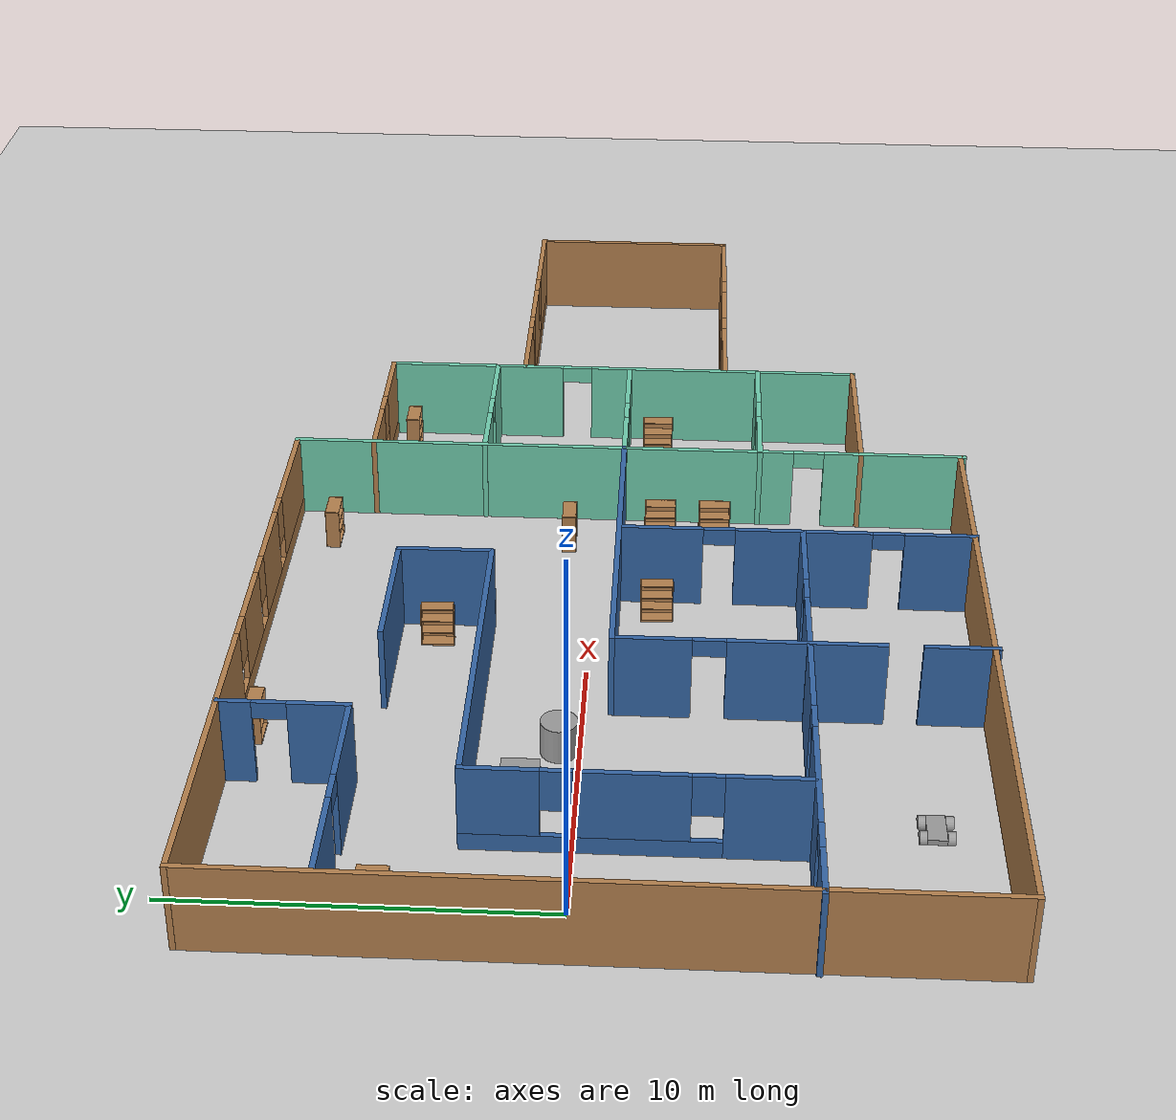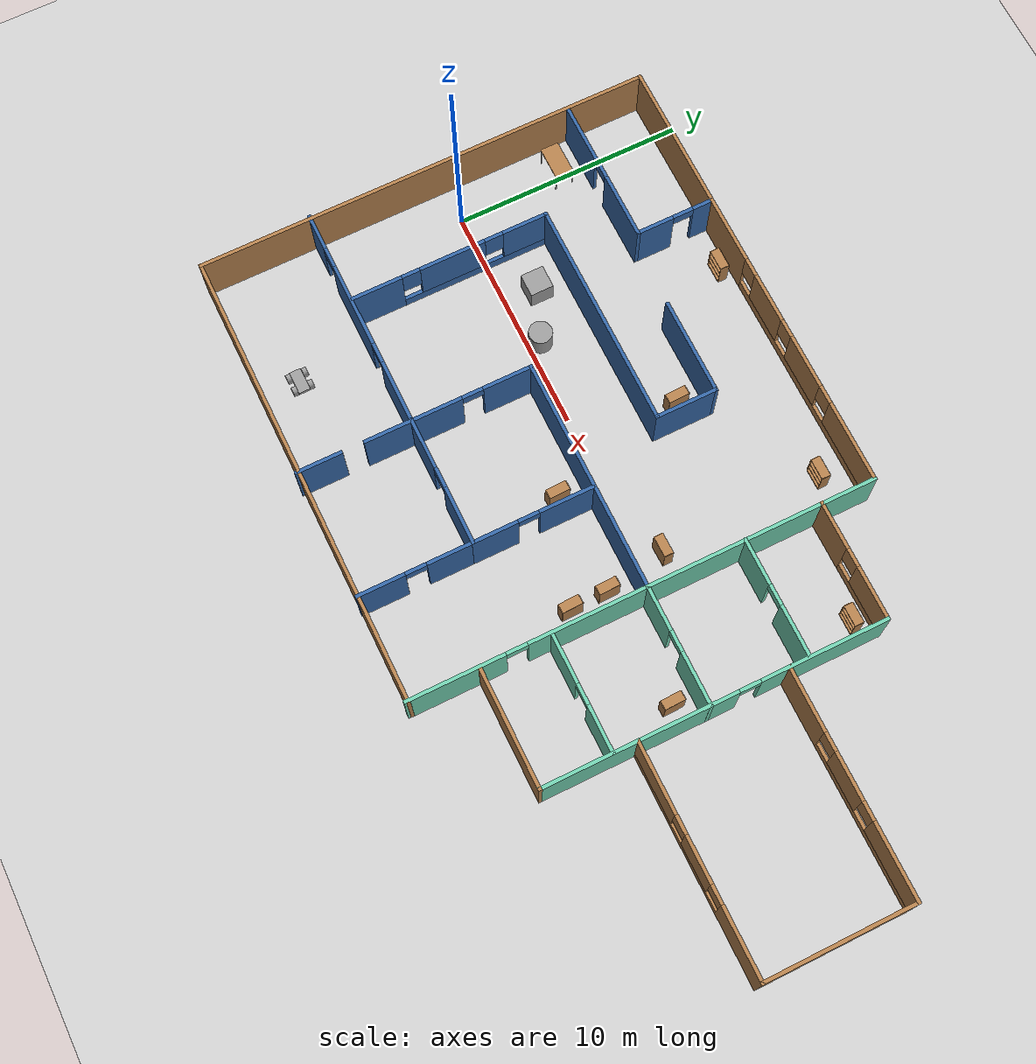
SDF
<sdf version="1.7">
 <world name="default">
  <plugin name="hello" filename="libhello.so"/>
  <light name="sun" type="directional">
   <pose>0 0 10 0 -0 0</pose>
   <diffuse>0.8 0.8 0.8 1</diffuse>
   <specular>0.2 0.2 0.2 1</specular>
   <attenuation>
    <range>1000</range>
    <constant>0.9</constant>
    <linear>0.01</linear>
    <quadratic>0.001</quadratic>
   </attenuation>
   <direction>-0.5 0.1 -0.9</direction>
   <spot><inner_angle>0</inner_angle><outer_angle>0</outer_angle><falloff>0</falloff></spot>
  </light>
  <model name="ground_plane">
   <static>1</static>
   <link name="link">
    <collision name="collision">
     <geometry><plane><normal>0 0 1</normal><size>100 100</size></plane></geometry>
     <surface>
      <contact><collide_bitmask>65535</collide_bitmask></contact>
      <friction><ode><mu>100</mu><mu2>50</mu2></ode></friction>
     </surface>
    </collision>
    <visual name="visual">
     <cast_shadows>0</cast_shadows>
     <geometry><plane><normal>0 0 1</normal><size>100 100</size></plane></geometry>
     <material>
      <script><uri>file://media/materials/scripts/gazebo.material</uri><name>Gazebo/Grey</name></script>
     </material>
    </visual>
   </link>
  </model>
  <gravity>0 0 -9.8</gravity>
  <magnetic_field>6e-06 2.3e-05 -4.2e-05</magnetic_field>
  <atmosphere type="adiabatic"/>
  <physics type="ode">
   <max_step_size>0.001</max_step_size>
   <real_time_factor>1</real_time_factor>
   <real_time_update_rate>1000</real_time_update_rate>
  </physics>
  <scene><ambient>0.4 0.4 0.4 1</ambient><background>0.7 0.7 0.7 1</background><shadows>1</shadows></scene>
  <spherical_coordinates>
   <surface_model>EARTH_WGS84</surface_model>
   <latitude_deg>0</latitude_deg>
   <longitude_deg>0</longitude_deg>
   <elevation>0</elevation>
   <heading_deg>0</heading_deg>
  </spherical_coordinates>
  <model name="lab">
   <pose>15.5975 -0.861877 0 0 -0 0</pose>
   <link name="Wall_23">
    <collision name="Wall_23_Collision">
     <geometry><box><size>10.2 0.15 2.5</size></box></geometry>
     <pose>0 0 1.25 0 -0 0</pose>
    </collision>
    <visual name="Wall_23_Visual">
     <pose>0 0 1.25 0 -0 0</pose>
     <geometry><box><size>10.2 0.15 2.5</size></box></geometry>
     <material>
      <script><uri>file://media/materials/scripts/gazebo.material</uri><name>Gazebo/Grey</name></script>
      <ambient>0.203922 0.396078 0.643137 1</ambient>
     </material>
     <meta><layer>0</layer></meta>
    </visual>
    <pose>-2.41254 0.125 0 0 -0 3.14159</pose>
   </link>
   <link name="Wall_29">
    <pose>2.61246 -4.925 0 0 -0 -1.5708</pose>
    <visual name="Wall_29_Visual_0">
     <pose>-2.55908 0 1.25 0 -0 0</pose>
     <geometry><box><size>5.13184 0.15 2.5</size></box></geometry>
     <material>
      <script><uri>file://media/materials/scripts/gazebo.material</uri><name>Gazebo/Grey</name></script>
      <ambient>0.435294 0.796078 0.67451 1</ambient>
     </material>
     <meta><layer>0</layer></meta>
    </visual>
    <collision name="Wall_29_Collision_0">
     <geometry><box><size>5.13184 0.15 2.5</size></box></geometry>
     <pose>-2.55908 0 1.25 0 -0 0</pose>
    </collision>
    <visual name="Wall_29_Visual_1">
     <pose>3.01592 0 1.25 0 -0 0</pose>
     <geometry><box><size>4.21816 0.15 2.5</size></box></geometry>
     <material>
      <script><uri>file://media/materials/scripts/gazebo.material</uri><name>Gazebo/Grey</name></script>
      <ambient>0.435294 0.796078 0.67451 1</ambient>
     </material>
     <meta><layer>0</layer></meta>
    </visual>
    <collision name="Wall_29_Collision_1">
     <geometry><box><size>4.21816 0.15 2.5</size></box></geometry>
     <pose>3.01592 0 1.25 0 -0 0</pose>
    </collision>
    <visual name="Wall_29_Visual_2">
     <pose>0.456844 0 2.25 0 -0 0</pose>
     <geometry><box><size>0.9 0.15 0.5</size></box></geometry>
     <material>
      <script><uri>file://media/materials/scripts/gazebo.material</uri><name>Gazebo/Grey</name></script>
      <ambient>0.435294 0.796078 0.67451 1</ambient>
     </material>
     <meta><layer>0</layer></meta>
    </visual>
    <collision name="Wall_29_Collision_2">
     <geometry><box><size>0.9 0.15 0.5</size></box></geometry>
     <pose>0.456844 0 2.25 0 -0 0</pose>
    </collision>
   </link>
   <link name="Wall_31">
    <collision name="Wall_31_Collision">
     <geometry><box><size>20 0.15 2.5</size></box></geometry>
     <pose>0 0 1.25 0 -0 0</pose>
    </collision>
    <visual name="Wall_31_Visual">
     <pose>0 0 1.25 0 -0 0</pose>
     <geometry><box><size>20 0.15 2.5</size></box></geometry>
     <material>
      <script><uri>file://media/materials/scripts/gazebo.material</uri><name>Gazebo/Wood</name></script>
      <ambient>1 1 1 1</ambient>
     </material>
     <meta><layer>0</layer></meta>
    </visual>
    <pose>-7.31254 -9.875 0 0 -0 0</pose>
   </link>
   <link name="Wall_33">
    <pose>-7.43754 -4.925 0 0 -0 -1.5708</pose>
    <visual name="Wall_33_Visual_0">
     <pose>-4.0304 0 1.25 0 -0 0</pose>
     <geometry><box><size>2.18921 0.15 2.5</size></box></geometry>
     <material>
      <script><uri>file://media/materials/scripts/gazebo.material</uri><name>Gazebo/Grey</name></script>
      <ambient>0.203922 0.396078 0.643137 1</ambient>
     </material>
     <meta><layer>0</layer></meta>
    </visual>
    <collision name="Wall_33_Collision_0">
     <geometry><box><size>2.18921 0.15 2.5</size></box></geometry>
     <pose>-4.0304 0 1.25 0 -0 0</pose>
    </collision>
    <visual name="Wall_33_Visual_1">
     <pose>0.082327 0 1.25 0 -0 0</pose>
     <geometry><box><size>4.23624 0.15 2.5</size></box></geometry>
     <material>
      <script><uri>file://media/materials/scripts/gazebo.material</uri><name>Gazebo/Grey</name></script>
      <ambient>0.203922 0.396078 0.643137 1</ambient>
     </material>
     <meta><layer>0</layer></meta>
    </visual>
    <collision name="Wall_33_Collision_1">
     <geometry><box><size>4.23624 0.15 2.5</size></box></geometry>
     <pose>0.082327 0 1.25 0 -0 0</pose>
    </collision>
    <visual name="Wall_33_Visual_2">
     <pose>4.11272 0 1.25 0 -0 0</pose>
     <geometry><box><size>2.02455 0.15 2.5</size></box></geometry>
     <material>
      <script><uri>file://media/materials/scripts/gazebo.material</uri><name>Gazebo/Grey</name></script>
      <ambient>0.203922 0.396078 0.643137 1</ambient>
     </material>
     <meta><layer>0</layer></meta>
    </visual>
    <collision name="Wall_33_Collision_2">
     <geometry><box><size>2.02455 0.15 2.5</size></box></geometry>
     <pose>4.11272 0 1.25 0 -0 0</pose>
    </collision>
    <visual name="Wall_33_Visual_3">
     <pose>-2.48579 0 2.25 0 -0 0</pose>
     <geometry><box><size>0.9 0.15 0.5</size></box></geometry>
     <material>
      <script><uri>file://media/materials/scripts/gazebo.material</uri><name>Gazebo/Grey</name></script>
      <ambient>0.203922 0.396078 0.643137 1</ambient>
     </material>
     <meta><layer>0</layer></meta>
    </visual>
    <collision name="Wall_33_Collision_3">
     <geometry><box><size>0.9 0.15 0.5</size></box></geometry>
     <pose>-2.48579 0 2.25 0 -0 0</pose>
    </collision>
    <visual name="Wall_33_Visual_4">
     <pose>2.20045 0 2.25 0 -0 0</pose>
     <geometry><box><size>0 0.15 0.5</size></box></geometry>
     <material>
      <script><uri>file://media/materials/scripts/gazebo.material</uri><name>Gazebo/Grey</name></script>
      <ambient>0.203922 0.396078 0.643137 1</ambient>
     </material>
     <meta><layer>0</layer></meta>
    </visual>
    <collision name="Wall_33_Collision_4">
     <geometry><box><size>0 0.15 0.5</size></box></geometry>
     <pose>2.20045 0 2.25 0 -0 0</pose>
    </collision>
   </link>
   <link name="Wall_35">
    <pose>-4.67701 -5.06118 0 0 -0 0</pose>
    <visual name="Wall_35_Visual_0">
     <pose>-1.73152 0 1.25 0 -0 0</pose>
     <geometry><box><size>2.28696 0.15 2.5</size></box></geometry>
     <material>
      <script><uri>file://media/materials/scripts/gazebo.material</uri><name>Gazebo/Grey</name></script>
      <ambient>0.203922 0.396078 0.643137 1</ambient>
     </material>
     <meta><layer>0</layer></meta>
    </visual>
    <collision name="Wall_35_Collision_0">
     <geometry><box><size>2.28696 0.15 2.5</size></box></geometry>
     <pose>-1.73152 0 1.25 0 -0 0</pose>
    </collision>
    <visual name="Wall_35_Visual_1">
     <pose>1.59348 0 1.25 0 -0 0</pose>
     <geometry><box><size>2.56304 0.15 2.5</size></box></geometry>
     <material>
      <script><uri>file://media/materials/scripts/gazebo.material</uri><name>Gazebo/Grey</name></script>
      <ambient>0.203922 0.396078 0.643137 1</ambient>
     </material>
     <meta><layer>0</layer></meta>
    </visual>
    <collision name="Wall_35_Collision_1">
     <geometry><box><size>2.56304 0.15 2.5</size></box></geometry>
     <pose>1.59348 0 1.25 0 -0 0</pose>
    </collision>
    <visual name="Wall_35_Visual_2">
     <pose>-0.138039 0 2.25 0 -0 0</pose>
     <geometry><box><size>0.9 0.15 0.5</size></box></geometry>
     <material>
      <script><uri>file://media/materials/scripts/gazebo.material</uri><name>Gazebo/Grey</name></script>
      <ambient>0.203922 0.396078 0.643137 1</ambient>
     </material>
     <meta><layer>0</layer></meta>
    </visual>
    <collision name="Wall_35_Collision_2">
     <geometry><box><size>0.9 0.15 0.5</size></box></geometry>
     <pose>-0.138039 0 2.25 0 -0 0</pose>
    </collision>
   </link>
   <link name="Wall_36">
    <pose>-1.87701 -2.51118 0 0 -0 1.5708</pose>
    <visual name="Wall_36_Visual_0">
     <pose>-1.63527 0 1.25 0 -0 0</pose>
     <geometry><box><size>1.97946 0.15 2.5</size></box></geometry>
     <material>
      <script><uri>file://media/materials/scripts/gazebo.material</uri><name>Gazebo/Grey</name></script>
      <ambient>0.203922 0.396078 0.643137 1</ambient>
     </material>
     <meta><layer>0</layer></meta>
    </visual>
    <collision name="Wall_36_Collision_0">
     <geometry><box><size>1.97946 0.15 2.5</size></box></geometry>
     <pose>-1.63527 0 1.25 0 -0 0</pose>
    </collision>
    <visual name="Wall_36_Visual_1">
     <pose>1.43973 0 1.25 0 -0 0</pose>
     <geometry><box><size>2.37054 0.15 2.5</size></box></geometry>
     <material>
      <script><uri>file://media/materials/scripts/gazebo.material</uri><name>Gazebo/Grey</name></script>
      <ambient>0.203922 0.396078 0.643137 1</ambient>
     </material>
     <meta><layer>0</layer></meta>
    </visual>
    <collision name="Wall_36_Collision_1">
     <geometry><box><size>2.37054 0.15 2.5</size></box></geometry>
     <pose>1.43973 0 1.25 0 -0 0</pose>
    </collision>
    <visual name="Wall_36_Visual_2">
     <pose>-0.195537 0 2.25 0 -0 0</pose>
     <geometry><box><size>0.9 0.15 0.5</size></box></geometry>
     <material>
      <script><uri>file://media/materials/scripts/gazebo.material</uri><name>Gazebo/Grey</name></script>
      <ambient>0.203922 0.396078 0.643137 1</ambient>
     </material>
     <meta><layer>0</layer></meta>
    </visual>
    <collision name="Wall_36_Collision_2">
     <geometry><box><size>0.9 0.15 0.5</size></box></geometry>
     <pose>-0.195537 0 2.25 0 -0 0</pose>
    </collision>
   </link>
   <link name="Wall_38">
    <pose>-1.87701 -7.48618 0 0 -0 -1.5708</pose>
    <visual name="Wall_38_Visual_0">
     <pose>-1.48387 0 1.25 0 -0 0</pose>
     <geometry><box><size>2.03226 0.15 2.5</size></box></geometry>
     <material>
      <script><uri>file://media/materials/scripts/gazebo.material</uri><name>Gazebo/Grey</name></script>
      <ambient>0.203922 0.396078 0.643137 1</ambient>
     </material>
     <meta><layer>0</layer></meta>
    </visual>
    <collision name="Wall_38_Collision_0">
     <geometry><box><size>2.03226 0.15 2.5</size></box></geometry>
     <pose>-1.48387 0 1.25 0 -0 0</pose>
    </collision>
    <visual name="Wall_38_Visual_1">
     <pose>1.46613 0 1.25 0 -0 0</pose>
     <geometry><box><size>2.06774 0.15 2.5</size></box></geometry>
     <material>
      <script><uri>file://media/materials/scripts/gazebo.material</uri><name>Gazebo/Grey</name></script>
      <ambient>0.203922 0.396078 0.643137 1</ambient>
     </material>
     <meta><layer>0</layer></meta>
    </visual>
    <collision name="Wall_38_Collision_1">
     <geometry><box><size>2.06774 0.15 2.5</size></box></geometry>
     <pose>1.46613 0 1.25 0 -0 0</pose>
    </collision>
    <visual name="Wall_38_Visual_2">
     <pose>-0.01774 0 2.25 0 -0 0</pose>
     <geometry><box><size>0.9 0.15 0.5</size></box></geometry>
     <material>
      <script><uri>file://media/materials/scripts/gazebo.material</uri><name>Gazebo/Grey</name></script>
      <ambient>0.203922 0.396078 0.643137 1</ambient>
     </material>
     <meta><layer>0</layer></meta>
    </visual>
    <collision name="Wall_38_Collision_2">
     <geometry><box><size>0.9 0.15 0.5</size></box></geometry>
     <pose>-0.01774 0 2.25 0 -0 0</pose>
    </collision>
   </link>
   <link name="Wall_40">
    <pose>-12.402 -5.06118 0 0 -0 3.14159</pose>
    <visual name="Wall_40_Visual_0">
     <pose>-3.60259 0 1.25 0 -0 0</pose>
     <geometry><box><size>2.79481 0.15 2.5</size></box></geometry>
     <material>
      <script><uri>file://media/materials/scripts/gazebo.material</uri><name>Gazebo/Grey</name></script>
      <ambient>0.203922 0.396078 0.643137 1</ambient>
     </material>
     <meta><layer>0</layer></meta>
    </visual>
    <collision name="Wall_40_Collision_0">
     <geometry><box><size>2.79481 0.15 2.5</size></box></geometry>
     <pose>-3.60259 0 1.25 0 -0 0</pose>
    </collision>
    <visual name="Wall_40_Visual_1">
     <pose>0.57217 0 1.25 0 -0 0</pose>
     <geometry><box><size>3.75472 0.15 2.5</size></box></geometry>
     <material>
      <script><uri>file://media/materials/scripts/gazebo.material</uri><name>Gazebo/Grey</name></script>
      <ambient>0.203922 0.396078 0.643137 1</ambient>
     </material>
     <meta><layer>0</layer></meta>
    </visual>
    <collision name="Wall_40_Collision_1">
     <geometry><box><size>3.75472 0.15 2.5</size></box></geometry>
     <pose>0.57217 0 1.25 0 -0 0</pose>
    </collision>
    <visual name="Wall_40_Visual_2">
     <pose>4.17476 0 1.25 0 -0 0</pose>
     <geometry><box><size>1.65047 0.15 2.5</size></box></geometry>
     <material>
      <script><uri>file://media/materials/scripts/gazebo.material</uri><name>Gazebo/Grey</name></script>
      <ambient>0.203922 0.396078 0.643137 1</ambient>
     </material>
     <meta><layer>0</layer></meta>
    </visual>
    <collision name="Wall_40_Collision_2">
     <geometry><box><size>1.65047 0.15 2.5</size></box></geometry>
     <pose>4.17476 0 1.25 0 -0 0</pose>
    </collision>
    <visual name="Wall_40_Visual_3">
     <pose>-1.75519 0 2.25 0 -0 0</pose>
     <geometry><box><size>0.9 0.15 0.5</size></box></geometry>
     <material>
      <script><uri>file://media/materials/scripts/gazebo.material</uri><name>Gazebo/Grey</name></script>
      <ambient>0.203922 0.396078 0.643137 1</ambient>
     </material>
     <meta><layer>0</layer></meta>
    </visual>
    <collision name="Wall_40_Collision_3">
     <geometry><box><size>0.9 0.15 0.5</size></box></geometry>
     <pose>-1.75519 0 2.25 0 -0 0</pose>
    </collision>
    <visual name="Wall_40_Visual_4">
     <pose>2.89953 0 2.25 0 -0 0</pose>
     <geometry><box><size>0.9 0.15 0.5</size></box></geometry>
     <material>
      <script><uri>file://media/materials/scripts/gazebo.material</uri><name>Gazebo/Grey</name></script>
      <ambient>0.203922 0.396078 0.643137 1</ambient>
     </material>
     <meta><layer>0</layer></meta>
    </visual>
    <collision name="Wall_40_Collision_4">
     <geometry><box><size>0.9 0.15 0.5</size></box></geometry>
     <pose>2.89953 0 2.25 0 -0 0</pose>
    </collision>
   </link>
   <link name="Wall_49">
    <pose>-13.22 -0.686186 0 0 -0 1.5708</pose>
    <visual name="Wall_49_Visual_0">
     <pose>-3.26401 0 1.25 0 -0 0</pose>
     <geometry><box><size>2.22198 0.15 2.5</size></box></geometry>
     <material>
      <script><uri>file://media/materials/scripts/gazebo.material</uri><name>Gazebo/Grey</name></script>
      <ambient>0.203922 0.396078 0.643137 1</ambient>
     </material>
     <meta><layer>0</layer></meta>
    </visual>
    <collision name="Wall_49_Collision_0">
     <geometry><box><size>2.22198 0.15 2.5</size></box></geometry>
     <pose>-3.26401 0 1.25 0 -0 0</pose>
    </collision>
    <visual name="Wall_49_Visual_1">
     <pose>1.11099 0 0.25 0 -0 0</pose>
     <geometry><box><size>6.52802 0.15 0.5</size></box></geometry>
     <material>
      <script><uri>file://media/materials/scripts/gazebo.material</uri><name>Gazebo/Grey</name></script>
      <ambient>0.203922 0.396078 0.643137 1</ambient>
     </material>
     <meta><layer>0</layer></meta>
    </visual>
    <collision name="Wall_49_Collision_1">
     <geometry><box><size>6.52802 0.15 0.5</size></box></geometry>
     <pose>1.11099 0 0.25 0 -0 0</pose>
    </collision>
    <visual name="Wall_49_Visual_2">
     <pose>0.092815 0 1.5 0 -0 0</pose>
     <geometry><box><size>2.89167 0.15 2</size></box></geometry>
     <material>
      <script><uri>file://media/materials/scripts/gazebo.material</uri><name>Gazebo/Grey</name></script>
      <ambient>0.203922 0.396078 0.643137 1</ambient>
     </material>
     <meta><layer>0</layer></meta>
    </visual>
    <collision name="Wall_49_Collision_2">
     <geometry><box><size>2.89167 0.15 2</size></box></geometry>
     <pose>0.092815 0 1.5 0 -0 0</pose>
    </collision>
    <visual name="Wall_49_Visual_3">
     <pose>3.35683 0 1.5 0 -0 0</pose>
     <geometry><box><size>2.03635 0.15 2</size></box></geometry>
     <material>
      <script><uri>file://media/materials/scripts/gazebo.material</uri><name>Gazebo/Grey</name></script>
      <ambient>0.203922 0.396078 0.643137 1</ambient>
     </material>
     <meta><layer>0</layer></meta>
    </visual>
    <collision name="Wall_49_Collision_3">
     <geometry><box><size>2.03635 0.15 2</size></box></geometry>
     <pose>3.35683 0 1.5 0 -0 0</pose>
    </collision>
    <visual name="Wall_49_Visual_4">
     <pose>-1.75302 0 1.9 0 -0 0</pose>
     <geometry><box><size>0.8 0.15 1.2</size></box></geometry>
     <material>
      <script><uri>file://media/materials/scripts/gazebo.material</uri><name>Gazebo/Grey</name></script>
      <ambient>0.203922 0.396078 0.643137 1</ambient>
     </material>
     <meta><layer>0</layer></meta>
    </visual>
    <collision name="Wall_49_Collision_4">
     <geometry><box><size>0.8 0.15 1.2</size></box></geometry>
     <pose>-1.75302 0 1.9 0 -0 0</pose>
    </collision>
    <visual name="Wall_49_Visual_5">
     <pose>1.93865 0 1.9 0 -0 0</pose>
     <geometry><box><size>0.8 0.15 1.2</size></box></geometry>
     <material>
      <script><uri>file://media/materials/scripts/gazebo.material</uri><name>Gazebo/Grey</name></script>
      <ambient>0.203922 0.396078 0.643137 1</ambient>
     </material>
     <meta><layer>0</layer></meta>
    </visual>
    <collision name="Wall_49_Collision_5">
     <geometry><box><size>0.8 0.15 1.2</size></box></geometry>
     <pose>1.93865 0 1.9 0 -0 0</pose>
    </collision>
   </link>
   <link name="Wall_5">
    <collision name="Wall_5_Collision">
     <geometry><box><size>20 0.15 2.5</size></box></geometry>
     <pose>0 0 1.25 0 -0 0</pose>
    </collision>
    <visual name="Wall_5_Visual">
     <pose>0 0 1.25 0 -0 0</pose>
     <geometry><box><size>20 0.15 2.5</size></box></geometry>
     <material>
      <script><uri>file://media/materials/scripts/gazebo.material</uri><name>Gazebo/Wood</name></script>
      <ambient>1 1 1 1</ambient>
     </material>
     <meta><layer>0</layer></meta>
    </visual>
    <pose>-17.2375 0.05 0 0 -0 -1.5708</pose>
   </link>
   <link name="Wall_50">
    <collision name="Wall_50_Collision">
     <geometry><box><size>10 0.15 2.5</size></box></geometry>
     <pose>0 0 1.25 0 -0 0</pose>
    </collision>
    <visual name="Wall_50_Visual">
     <pose>0 0 1.25 0 -0 0</pose>
     <geometry><box><size>10 0.15 2.5</size></box></geometry>
     <material>
      <script><uri>file://media/materials/scripts/gazebo.material</uri><name>Gazebo/Grey</name></script>
      <ambient>0.203922 0.396078 0.643137 1</ambient>
     </material>
     <meta><layer>0</layer></meta>
    </visual>
    <pose>-8.29501 3.61381 0 0 -0 0</pose>
   </link>
   <link name="Wall_51">
    <collision name="Wall_51_Collision">
     <geometry><box><size>2.75 0.15 2.5</size></box></geometry>
     <pose>0 0 1.25 0 -0 0</pose>
    </collision>
    <visual name="Wall_51_Visual">
     <pose>0 0 1.25 0 -0 0</pose>
     <geometry><box><size>2.75 0.15 2.5</size></box></geometry>
     <material>
      <script><uri>file://media/materials/scripts/gazebo.material</uri><name>Gazebo/Grey</name></script>
      <ambient>0.203922 0.396078 0.643137 1</ambient>
     </material>
     <meta><layer>0</layer></meta>
    </visual>
    <pose>-3.37001 4.91381 0 0 -0 1.5708</pose>
   </link>
   <link name="Wall_52">
    <collision name="Wall_52_Collision">
     <geometry><box><size>4.25 0.15 2.5</size></box></geometry>
     <pose>0 0 1.25 0 -0 0</pose>
    </collision>
    <visual name="Wall_52_Visual">
     <pose>0 0 1.25 0 -0 0</pose>
     <geometry><box><size>4.25 0.15 2.5</size></box></geometry>
     <material>
      <script><uri>file://media/materials/scripts/gazebo.material</uri><name>Gazebo/Grey</name></script>
      <ambient>0.203922 0.396078 0.643137 1</ambient>
     </material>
     <meta><layer>0</layer></meta>
    </visual>
    <pose>-5.42001 6.21381 0 0 -0 3.14159</pose>
   </link>
   <link name="Wall_54">
    <pose>-10.8124 8.26601 0 0 -0 -1.5708</pose>
    <visual name="Wall_54_Visual_0">
     <pose>-1.2849 0 1.25 0 -0 0</pose>
     <geometry><box><size>0.930201 0.15 2.5</size></box></geometry>
     <material>
      <script><uri>file://media/materials/scripts/gazebo.material</uri><name>Gazebo/Grey</name></script>
      <ambient>0.203922 0.396078 0.643137 1</ambient>
     </material>
     <meta><layer>0</layer></meta>
    </visual>
    <collision name="Wall_54_Collision_0">
     <geometry><box><size>0.930201 0.15 2.5</size></box></geometry>
     <pose>-1.2849 0 1.25 0 -0 0</pose>
    </collision>
    <visual name="Wall_54_Visual_1">
     <pose>0.915101 0 1.25 0 -0 0</pose>
     <geometry><box><size>1.6698 0.15 2.5</size></box></geometry>
     <material>
      <script><uri>file://media/materials/scripts/gazebo.material</uri><name>Gazebo/Grey</name></script>
      <ambient>0.203922 0.396078 0.643137 1</ambient>
     </material>
     <meta><layer>0</layer></meta>
    </visual>
    <collision name="Wall_54_Collision_1">
     <geometry><box><size>1.6698 0.15 2.5</size></box></geometry>
     <pose>0.915101 0 1.25 0 -0 0</pose>
    </collision>
    <visual name="Wall_54_Visual_2">
     <pose>-0.369799 0 2.25 0 -0 0</pose>
     <geometry><box><size>0.9 0.15 0.5</size></box></geometry>
     <material>
      <script><uri>file://media/materials/scripts/gazebo.material</uri><name>Gazebo/Grey</name></script>
      <ambient>0.203922 0.396078 0.643137 1</ambient>
     </material>
     <meta><layer>0</layer></meta>
    </visual>
    <collision name="Wall_54_Collision_2">
     <geometry><box><size>0.9 0.15 0.5</size></box></geometry>
     <pose>-0.369799 0 2.25 0 -0 0</pose>
    </collision>
   </link>
   <link name="Wall_55">
    <pose>-13.9874 6.59101 0 0 -0 3.14159</pose>
    <visual name="Wall_55_Visual_0">
     <pose>-1.78146 0 1.25 0 -0 0</pose>
     <geometry><box><size>2.93709 0.15 2.5</size></box></geometry>
     <material>
      <script><uri>file://media/materials/scripts/gazebo.material</uri><name>Gazebo/Grey</name></script>
      <ambient>0.203922 0.396078 0.643137 1</ambient>
     </material>
     <meta><layer>0</layer></meta>
    </visual>
    <collision name="Wall_55_Collision_0">
     <geometry><box><size>2.93709 0.15 2.5</size></box></geometry>
     <pose>-1.78146 0 1.25 0 -0 0</pose>
    </collision>
    <visual name="Wall_55_Visual_1">
     <pose>1.91854 0 1.25 0 -0 0</pose>
     <geometry><box><size>2.66291 0.15 2.5</size></box></geometry>
     <material>
      <script><uri>file://media/materials/scripts/gazebo.material</uri><name>Gazebo/Grey</name></script>
      <ambient>0.203922 0.396078 0.643137 1</ambient>
     </material>
     <meta><layer>0</layer></meta>
    </visual>
    <collision name="Wall_55_Collision_1">
     <geometry><box><size>2.66291 0.15 2.5</size></box></geometry>
     <pose>1.91854 0 1.25 0 -0 0</pose>
    </collision>
    <visual name="Wall_55_Visual_2">
     <pose>0.137089 0 2.25 0 -0 0</pose>
     <geometry><box><size>0.9 0.15 0.5</size></box></geometry>
     <material>
      <script><uri>file://media/materials/scripts/gazebo.material</uri><name>Gazebo/Grey</name></script>
      <ambient>0.203922 0.396078 0.643137 1</ambient>
     </material>
     <meta><layer>0</layer></meta>
    </visual>
    <collision name="Wall_55_Collision_2">
     <geometry><box><size>0.9 0.15 0.5</size></box></geometry>
     <pose>0.137089 0 2.25 0 -0 0</pose>
    </collision>
   </link>
   <link name="Wall_57">
    <pose>5.16025 7.66391 0 0 -0 0</pose>
    <visual name="Wall_57_Visual_0">
     <pose>-1.57792 0 1.25 0 -0 0</pose>
     <geometry><box><size>2.09416 0.15 2.5</size></box></geometry>
     <material>
      <script><uri>file://media/materials/scripts/gazebo.material</uri><name>Gazebo/Wood</name></script>
      <ambient>0.921569 0.807843 0.615686 1</ambient>
     </material>
     <meta><layer>0</layer></meta>
    </visual>
    <collision name="Wall_57_Collision_0">
     <geometry><box><size>2.09416 0.15 2.5</size></box></geometry>
     <pose>-1.57792 0 1.25 0 -0 0</pose>
    </collision>
    <visual name="Wall_57_Visual_1">
     <pose>1.04708 0 0.25 0 -0 0</pose>
     <geometry><box><size>3.15584 0.15 0.5</size></box></geometry>
     <material>
      <script><uri>file://media/materials/scripts/gazebo.material</uri><name>Gazebo/Wood</name></script>
      <ambient>0.921569 0.807843 0.615686 1</ambient>
     </material>
     <meta><layer>0</layer></meta>
    </visual>
    <collision name="Wall_57_Collision_1">
     <geometry><box><size>3.15584 0.15 0.5</size></box></geometry>
     <pose>1.04708 0 0.25 0 -0 0</pose>
    </collision>
    <visual name="Wall_57_Visual_2">
     <pose>1.44708 0 1.5 0 -0 0</pose>
     <geometry><box><size>2.35584 0.15 2</size></box></geometry>
     <material>
      <script><uri>file://media/materials/scripts/gazebo.material</uri><name>Gazebo/Wood</name></script>
      <ambient>0.921569 0.807843 0.615686 1</ambient>
     </material>
     <meta><layer>0</layer></meta>
    </visual>
    <collision name="Wall_57_Collision_2">
     <geometry><box><size>2.35584 0.15 2</size></box></geometry>
     <pose>1.44708 0 1.5 0 -0 0</pose>
    </collision>
    <visual name="Wall_57_Visual_3">
     <pose>-0.130837 0 1.9 0 -0 0</pose>
     <geometry><box><size>0.8 0.15 1.2</size></box></geometry>
     <material>
      <script><uri>file://media/materials/scripts/gazebo.material</uri><name>Gazebo/Wood</name></script>
      <ambient>0.921569 0.807843 0.615686 1</ambient>
     </material>
     <meta><layer>0</layer></meta>
    </visual>
    <collision name="Wall_57_Collision_3">
     <geometry><box><size>0.8 0.15 1.2</size></box></geometry>
     <pose>-0.130837 0 1.9 0 -0 0</pose>
    </collision>
   </link>
   <link name="Wall_58">
    <pose>7.71025 0.363913 0 0 -0 -1.5708</pose>
    <visual name="Wall_58_Visual_0">
     <pose>-4.62429 0 1.25 0 -0 0</pose>
     <geometry><box><size>5.50142 0.15 2.5</size></box></geometry>
     <material>
      <script><uri>file://media/materials/scripts/gazebo.material</uri><name>Gazebo/Grey</name></script>
      <ambient>0.435294 0.796078 0.67451 1</ambient>
     </material>
     <meta><layer>0</layer></meta>
    </visual>
    <collision name="Wall_58_Collision_0">
     <geometry><box><size>5.50142 0.15 2.5</size></box></geometry>
     <pose>-4.62429 0 1.25 0 -0 0</pose>
    </collision>
    <visual name="Wall_58_Visual_1">
     <pose>3.20071 0 1.25 0 -0 0</pose>
     <geometry><box><size>8.34858 0.15 2.5</size></box></geometry>
     <material>
      <script><uri>file://media/materials/scripts/gazebo.material</uri><name>Gazebo/Grey</name></script>
      <ambient>0.435294 0.796078 0.67451 1</ambient>
     </material>
     <meta><layer>0</layer></meta>
    </visual>
    <collision name="Wall_58_Collision_1">
     <geometry><box><size>8.34858 0.15 2.5</size></box></geometry>
     <pose>3.20071 0 1.25 0 -0 0</pose>
    </collision>
    <visual name="Wall_58_Visual_2">
     <pose>-1.42358 0 2.25 0 -0 0</pose>
     <geometry><box><size>0.9 0.15 0.5</size></box></geometry>
     <material>
      <script><uri>file://media/materials/scripts/gazebo.material</uri><name>Gazebo/Grey</name></script>
      <ambient>0.435294 0.796078 0.67451 1</ambient>
     </material>
     <meta><layer>0</layer></meta>
    </visual>
    <collision name="Wall_58_Collision_2">
     <geometry><box><size>0.9 0.15 0.5</size></box></geometry>
     <pose>-1.42358 0 2.25 0 -0 0</pose>
    </collision>
   </link>
   <link name="Wall_59">
    <collision name="Wall_59_Collision">
     <geometry><box><size>5.25 0.15 2.5</size></box></geometry>
     <pose>0 0 1.25 0 -0 0</pose>
    </collision>
    <visual name="Wall_59_Visual">
     <pose>0 0 1.25 0 -0 0</pose>
     <geometry><box><size>5.25 0.15 2.5</size></box></geometry>
     <material>
      <script><uri>file://media/materials/scripts/gazebo.material</uri><name>Gazebo/Wood</name></script>
      <ambient>1 1 1 1</ambient>
     </material>
     <meta><layer>0</layer></meta>
    </visual>
    <pose>5.16025 -6.93609 0 0 -0 3.14159</pose>
   </link>
   <link name="Wall_61">
    <pose>5.15095 4.32005 0 0 -0 0</pose>
    <visual name="Wall_61_Visual_0">
     <pose>-1.59827 0 1.25 0 -0 0</pose>
     <geometry><box><size>2.05346 0.15 2.5</size></box></geometry>
     <material>
      <script><uri>file://media/materials/scripts/gazebo.material</uri><name>Gazebo/Grey</name></script>
      <ambient>0.435294 0.796078 0.67451 1</ambient>
     </material>
     <meta><layer>0</layer></meta>
    </visual>
    <collision name="Wall_61_Collision_0">
     <geometry><box><size>2.05346 0.15 2.5</size></box></geometry>
     <pose>-1.59827 0 1.25 0 -0 0</pose>
    </collision>
    <visual name="Wall_61_Visual_1">
     <pose>1.47673 0 1.25 0 -0 0</pose>
     <geometry><box><size>2.29654 0.15 2.5</size></box></geometry>
     <material>
      <script><uri>file://media/materials/scripts/gazebo.material</uri><name>Gazebo/Grey</name></script>
      <ambient>0.435294 0.796078 0.67451 1</ambient>
     </material>
     <meta><layer>0</layer></meta>
    </visual>
    <collision name="Wall_61_Collision_1">
     <geometry><box><size>2.29654 0.15 2.5</size></box></geometry>
     <pose>1.47673 0 1.25 0 -0 0</pose>
    </collision>
    <visual name="Wall_61_Visual_2">
     <pose>-0.12154 0 2.25 0 -0 0</pose>
     <geometry><box><size>0.9 0.15 0.5</size></box></geometry>
     <material>
      <script><uri>file://media/materials/scripts/gazebo.material</uri><name>Gazebo/Grey</name></script>
      <ambient>0.435294 0.796078 0.67451 1</ambient>
     </material>
     <meta><layer>0</layer></meta>
    </visual>
    <collision name="Wall_61_Collision_2">
     <geometry><box><size>0.9 0.15 0.5</size></box></geometry>
     <pose>-0.12154 0 2.25 0 -0 0</pose>
    </collision>
   </link>
   <link name="Wall_63">
    <pose>5.16247 0.125 0 0 -0 0</pose>
    <visual name="Wall_63_Visual_0">
     <pose>-1.63078 0 1.25 0 -0 0</pose>
     <geometry><box><size>1.98844 0.15 2.5</size></box></geometry>
     <material>
      <script><uri>file://media/materials/scripts/gazebo.material</uri><name>Gazebo/Grey</name></script>
      <ambient>0.435294 0.796078 0.67451 1</ambient>
     </material>
     <meta><layer>0</layer></meta>
    </visual>
    <collision name="Wall_63_Collision_0">
     <geometry><box><size>1.98844 0.15 2.5</size></box></geometry>
     <pose>-1.63078 0 1.25 0 -0 0</pose>
    </collision>
    <visual name="Wall_63_Visual_1">
     <pose>1.44422 0 1.25 0 -0 0</pose>
     <geometry><box><size>2.36156 0.15 2.5</size></box></geometry>
     <material>
      <script><uri>file://media/materials/scripts/gazebo.material</uri><name>Gazebo/Grey</name></script>
      <ambient>0.435294 0.796078 0.67451 1</ambient>
     </material>
     <meta><layer>0</layer></meta>
    </visual>
    <collision name="Wall_63_Collision_1">
     <geometry><box><size>2.36156 0.15 2.5</size></box></geometry>
     <pose>1.44422 0 1.25 0 -0 0</pose>
    </collision>
    <visual name="Wall_63_Visual_2">
     <pose>-0.186559 0 2.25 0 -0 0</pose>
     <geometry><box><size>0.9 0.15 0.5</size></box></geometry>
     <material>
      <script><uri>file://media/materials/scripts/gazebo.material</uri><name>Gazebo/Grey</name></script>
      <ambient>0.435294 0.796078 0.67451 1</ambient>
     </material>
     <meta><layer>0</layer></meta>
    </visual>
    <collision name="Wall_63_Collision_2">
     <geometry><box><size>0.9 0.15 0.5</size></box></geometry>
     <pose>-0.186559 0 2.25 0 -0 0</pose>
    </collision>
   </link>
   <link name="Wall_65">
    <pose>5.15095 -3.93288 0 0 -0 0</pose>
    <visual name="Wall_65_Visual_0">
     <pose>-1.49127 0 1.25 0 -0 0</pose>
     <geometry><box><size>2.26747 0.15 2.5</size></box></geometry>
     <material>
      <script><uri>file://media/materials/scripts/gazebo.material</uri><name>Gazebo/Grey</name></script>
      <ambient>0.435294 0.796078 0.67451 1</ambient>
     </material>
     <meta><layer>0</layer></meta>
    </visual>
    <collision name="Wall_65_Collision_0">
     <geometry><box><size>2.26747 0.15 2.5</size></box></geometry>
     <pose>-1.49127 0 1.25 0 -0 0</pose>
    </collision>
    <visual name="Wall_65_Visual_1">
     <pose>1.58373 0 1.25 0 -0 0</pose>
     <geometry><box><size>2.08253 0.15 2.5</size></box></geometry>
     <material>
      <script><uri>file://media/materials/scripts/gazebo.material</uri><name>Gazebo/Grey</name></script>
      <ambient>0.435294 0.796078 0.67451 1</ambient>
     </material>
     <meta><layer>0</layer></meta>
    </visual>
    <collision name="Wall_65_Collision_1">
     <geometry><box><size>2.08253 0.15 2.5</size></box></geometry>
     <pose>1.58373 0 1.25 0 -0 0</pose>
    </collision>
    <visual name="Wall_65_Visual_2">
     <pose>0.09247 0 2.25 0 -0 0</pose>
     <geometry><box><size>0.9 0.15 0.5</size></box></geometry>
     <material>
      <script><uri>file://media/materials/scripts/gazebo.material</uri><name>Gazebo/Grey</name></script>
      <ambient>0.435294 0.796078 0.67451 1</ambient>
     </material>
     <meta><layer>0</layer></meta>
    </visual>
    <collision name="Wall_65_Collision_2">
     <geometry><box><size>0.9 0.15 0.5</size></box></geometry>
     <pose>0.09247 0 2.25 0 -0 0</pose>
    </collision>
   </link>
   <link name="Wall_67">
    <pose>12.527 3.45056 0 0 -0 0</pose>
    <visual name="Wall_67_Visual_0">
     <pose>-3.47042 0 1.25 0 -0 0</pose>
     <geometry><box><size>2.80917 0.15 2.5</size></box></geometry>
     <material>
      <script><uri>file://media/materials/scripts/gazebo.material</uri><name>Gazebo/Wood</name></script>
      <ambient>1 1 1 1</ambient>
     </material>
     <meta><layer>0</layer></meta>
    </visual>
    <collision name="Wall_67_Collision_0">
     <geometry><box><size>2.80917 0.15 2.5</size></box></geometry>
     <pose>-3.47042 0 1.25 0 -0 0</pose>
    </collision>
    <visual name="Wall_67_Visual_1">
     <pose>1.40458 0 0.25 0 -0 0</pose>
     <geometry><box><size>6.94083 0.15 0.5</size></box></geometry>
     <material>
      <script><uri>file://media/materials/scripts/gazebo.material</uri><name>Gazebo/Wood</name></script>
      <ambient>1 1 1 1</ambient>
     </material>
     <meta><layer>0</layer></meta>
    </visual>
    <collision name="Wall_67_Collision_1">
     <geometry><box><size>6.94083 0.15 0.5</size></box></geometry>
     <pose>1.40458 0 0.25 0 -0 0</pose>
    </collision>
    <visual name="Wall_67_Visual_2">
     <pose>-0.248014 0 1.5 0 -0 0</pose>
     <geometry><box><size>2.03563 0.15 2</size></box></geometry>
     <material>
      <script><uri>file://media/materials/scripts/gazebo.material</uri><name>Gazebo/Wood</name></script>
      <ambient>1 1 1 1</ambient>
     </material>
     <meta><layer>0</layer></meta>
    </visual>
    <collision name="Wall_67_Collision_2">
     <geometry><box><size>2.03563 0.15 2</size></box></geometry>
     <pose>-0.248014 0 1.5 0 -0 0</pose>
    </collision>
    <visual name="Wall_67_Visual_3">
     <pose>3.2224 0 1.5 0 -0 0</pose>
     <geometry><box><size>3.3052 0.15 2</size></box></geometry>
     <material>
      <script><uri>file://media/materials/scripts/gazebo.material</uri><name>Gazebo/Wood</name></script>
      <ambient>1 1 1 1</ambient>
     </material>
     <meta><layer>0</layer></meta>
    </visual>
    <collision name="Wall_67_Collision_3">
     <geometry><box><size>3.3052 0.15 2</size></box></geometry>
     <pose>3.2224 0 1.5 0 -0 0</pose>
    </collision>
    <visual name="Wall_67_Visual_4">
     <pose>-1.66583 0 1.9 0 -0 0</pose>
     <geometry><box><size>0.8 0.15 1.2</size></box></geometry>
     <material>
      <script><uri>file://media/materials/scripts/gazebo.material</uri><name>Gazebo/Wood</name></script>
      <ambient>1 1 1 1</ambient>
     </material>
     <meta><layer>0</layer></meta>
    </visual>
    <collision name="Wall_67_Collision_4">
     <geometry><box><size>0.8 0.15 1.2</size></box></geometry>
     <pose>-1.66583 0 1.9 0 -0 0</pose>
    </collision>
    <visual name="Wall_67_Visual_5">
     <pose>1.1698 0 1.9 0 -0 0</pose>
     <geometry><box><size>0.8 0.15 1.2</size></box></geometry>
     <material>
      <script><uri>file://media/materials/scripts/gazebo.material</uri><name>Gazebo/Wood</name></script>
      <ambient>1 1 1 1</ambient>
     </material>
     <meta><layer>0</layer></meta>
    </visual>
    <collision name="Wall_67_Collision_5">
     <geometry><box><size>0.8 0.15 1.2</size></box></geometry>
     <pose>1.1698 0 1.9 0 -0 0</pose>
    </collision>
   </link>
   <link name="Wall_68">
    <collision name="Wall_68_Collision">
     <geometry><box><size>6.5 0.15 2.5</size></box></geometry>
     <pose>0 0 1.25 0 -0 0</pose>
    </collision>
    <visual name="Wall_68_Visual">
     <pose>0 0 1.25 0 -0 0</pose>
     <geometry><box><size>6.5 0.15 2.5</size></box></geometry>
     <material>
      <script><uri>file://media/materials/scripts/gazebo.material</uri><name>Gazebo/Wood</name></script>
      <ambient>1 1 1 1</ambient>
     </material>
     <meta><layer>0</layer></meta>
    </visual>
    <pose>17.327 0.27556 0 0 -0 -1.5708</pose>
   </link>
   <link name="Wall_69">
    <pose>12.527 -2.89944 0 0 -0 3.14159</pose>
    <visual name="Wall_69_Visual_0">
     <pose>-3.32941 0 1.25 0 -0 0</pose>
     <geometry><box><size>3.09119 0.15 2.5</size></box></geometry>
     <material>
      <script><uri>file://media/materials/scripts/gazebo.material</uri><name>Gazebo/Wood</name></script>
      <ambient>1 1 1 1</ambient>
     </material>
     <meta><layer>0</layer></meta>
    </visual>
    <collision name="Wall_69_Collision_0">
     <geometry><box><size>3.09119 0.15 2.5</size></box></geometry>
     <pose>-3.32941 0 1.25 0 -0 0</pose>
    </collision>
    <visual name="Wall_69_Visual_1">
     <pose>1.54559 0 0.25 0 -0 0</pose>
     <geometry><box><size>6.65881 0.15 0.5</size></box></geometry>
     <material>
      <script><uri>file://media/materials/scripts/gazebo.material</uri><name>Gazebo/Wood</name></script>
      <ambient>1 1 1 1</ambient>
     </material>
     <meta><layer>0</layer></meta>
    </visual>
    <collision name="Wall_69_Collision_1">
     <geometry><box><size>6.65881 0.15 0.5</size></box></geometry>
     <pose>1.54559 0 0.25 0 -0 0</pose>
    </collision>
    <visual name="Wall_69_Visual_2">
     <pose>0.007252 0 1.5 0 -0 0</pose>
     <geometry><box><size>1.98213 0.15 2</size></box></geometry>
     <material>
      <script><uri>file://media/materials/scripts/gazebo.material</uri><name>Gazebo/Wood</name></script>
      <ambient>1 1 1 1</ambient>
     </material>
     <meta><layer>0</layer></meta>
    </visual>
    <collision name="Wall_69_Collision_2">
     <geometry><box><size>1.98213 0.15 2</size></box></geometry>
     <pose>0.007252 0 1.5 0 -0 0</pose>
    </collision>
    <visual name="Wall_69_Visual_3">
     <pose>3.33666 0 1.5 0 -0 0</pose>
     <geometry><box><size>3.07668 0.15 2</size></box></geometry>
     <material>
      <script><uri>file://media/materials/scripts/gazebo.material</uri><name>Gazebo/Wood</name></script>
      <ambient>1 1 1 1</ambient>
     </material>
     <meta><layer>0</layer></meta>
    </visual>
    <collision name="Wall_69_Collision_3">
     <geometry><box><size>3.07668 0.15 2</size></box></geometry>
     <pose>3.33666 0 1.5 0 -0 0</pose>
    </collision>
    <visual name="Wall_69_Visual_4">
     <pose>-1.38381 0 1.9 0 -0 0</pose>
     <geometry><box><size>0.8 0.15 1.2</size></box></geometry>
     <material>
      <script><uri>file://media/materials/scripts/gazebo.material</uri><name>Gazebo/Wood</name></script>
      <ambient>1 1 1 1</ambient>
     </material>
     <meta><layer>0</layer></meta>
    </visual>
    <collision name="Wall_69_Collision_4">
     <geometry><box><size>0.8 0.15 1.2</size></box></geometry>
     <pose>-1.38381 0 1.9 0 -0 0</pose>
    </collision>
    <visual name="Wall_69_Visual_5">
     <pose>1.39832 0 1.9 0 -0 0</pose>
     <geometry><box><size>0.8 0.15 1.2</size></box></geometry>
     <material>
      <script><uri>file://media/materials/scripts/gazebo.material</uri><name>Gazebo/Wood</name></script>
      <ambient>1 1 1 1</ambient>
     </material>
     <meta><layer>0</layer></meta>
    </visual>
    <collision name="Wall_69_Collision_5">
     <geometry><box><size>0.8 0.15 1.2</size></box></geometry>
     <pose>1.39832 0 1.9 0 -0 0</pose>
    </collision>
   </link>
   <link name="Wall_7">
    <pose>-7.31254 9.975 0 0 -0 0</pose>
    <visual name="Wall_7_Visual_0">
     <pose>-5.26207 0 1.25 0 -0 0</pose>
     <geometry><box><size>9.47586 0.15 2.5</size></box></geometry>
     <material>
      <script><uri>file://media/materials/scripts/gazebo.material</uri><name>Gazebo/Wood</name></script>
      <ambient>1 1 1 1</ambient>
     </material>
     <meta><layer>0</layer></meta>
    </visual>
    <collision name="Wall_7_Collision_0">
     <geometry><box><size>9.47586 0.15 2.5</size></box></geometry>
     <pose>-5.26207 0 1.25 0 -0 0</pose>
    </collision>
    <visual name="Wall_7_Visual_1">
     <pose>4.73793 0 0.25 0 -0 0</pose>
     <geometry><box><size>10.5241 0.15 0.5</size></box></geometry>
     <material>
      <script><uri>file://media/materials/scripts/gazebo.material</uri><name>Gazebo/Wood</name></script>
      <ambient>1 1 1 1</ambient>
     </material>
     <meta><layer>0</layer></meta>
    </visual>
    <collision name="Wall_7_Collision_1">
     <geometry><box><size>10.5241 0.15 0.5</size></box></geometry>
     <pose>4.73793 0 0.25 0 -0 0</pose>
    </collision>
    <visual name="Wall_7_Visual_2">
     <pose>1.37393 0 1.5 0 -0 0</pose>
     <geometry><box><size>2.19614 0.15 2</size></box></geometry>
     <material>
      <script><uri>file://media/materials/scripts/gazebo.material</uri><name>Gazebo/Wood</name></script>
      <ambient>1 1 1 1</ambient>
     </material>
     <meta><layer>0</layer></meta>
    </visual>
    <collision name="Wall_7_Collision_2">
     <geometry><box><size>2.19614 0.15 2</size></box></geometry>
     <pose>1.37393 0 1.5 0 -0 0</pose>
    </collision>
    <visual name="Wall_7_Visual_3">
     <pose>4.45033 0 1.5 0 -0 0</pose>
     <geometry><box><size>2.35665 0.15 2</size></box></geometry>
     <material>
      <script><uri>file://media/materials/scripts/gazebo.material</uri><name>Gazebo/Wood</name></script>
      <ambient>1 1 1 1</ambient>
     </material>
     <meta><layer>0</layer></meta>
    </visual>
    <collision name="Wall_7_Collision_3">
     <geometry><box><size>2.35665 0.15 2</size></box></geometry>
     <pose>4.45033 0 1.5 0 -0 0</pose>
    </collision>
    <visual name="Wall_7_Visual_4">
     <pose>8.21433 0 1.5 0 -0 0</pose>
     <geometry><box><size>3.57135 0.15 2</size></box></geometry>
     <material>
      <script><uri>file://media/materials/scripts/gazebo.material</uri><name>Gazebo/Wood</name></script>
      <ambient>1 1 1 1</ambient>
     </material>
     <meta><layer>0</layer></meta>
    </visual>
    <collision name="Wall_7_Collision_4">
     <geometry><box><size>3.57135 0.15 2</size></box></geometry>
     <pose>8.21433 0 1.5 0 -0 0</pose>
    </collision>
    <visual name="Wall_7_Visual_5">
     <pose>-0.124138 0 1.9 0 -0 0</pose>
     <geometry><box><size>0.8 0.15 1.2</size></box></geometry>
     <material>
      <script><uri>file://media/materials/scripts/gazebo.material</uri><name>Gazebo/Wood</name></script>
      <ambient>1 1 1 1</ambient>
     </material>
     <meta><layer>0</layer></meta>
    </visual>
    <collision name="Wall_7_Collision_5">
     <geometry><box><size>0.8 0.15 1.2</size></box></geometry>
     <pose>-0.124138 0 1.9 0 -0 0</pose>
    </collision>
    <visual name="Wall_7_Visual_6">
     <pose>2.872 0 1.9 0 -0 0</pose>
     <geometry><box><size>0.8 0.15 1.2</size></box></geometry>
     <material>
      <script><uri>file://media/materials/scripts/gazebo.material</uri><name>Gazebo/Wood</name></script>
      <ambient>1 1 1 1</ambient>
     </material>
     <meta><layer>0</layer></meta>
    </visual>
    <collision name="Wall_7_Collision_6">
     <geometry><box><size>0.8 0.15 1.2</size></box></geometry>
     <pose>2.872 0 1.9 0 -0 0</pose>
    </collision>
    <visual name="Wall_7_Visual_7">
     <pose>6.02865 0 1.9 0 -0 0</pose>
     <geometry><box><size>0.8 0.15 1.2</size></box></geometry>
     <material>
      <script><uri>file://media/materials/scripts/gazebo.material</uri><name>Gazebo/Wood</name></script>
      <ambient>1 1 1 1</ambient>
     </material>
     <meta><layer>0</layer></meta>
    </visual>
    <collision name="Wall_7_Collision_7">
     <geometry><box><size>0.8 0.15 1.2</size></box></geometry>
     <pose>6.02865 0 1.9 0 -0 0</pose>
    </collision>
   </link>
   <link name="Wall_9">
    <collision name="Wall_9_Collision">
     <geometry><box><size>10 0.15 2.5</size></box></geometry>
     <pose>0 0 1.25 0 -0 0</pose>
    </collision>
    <visual name="Wall_9_Visual">
     <pose>0 0 1.25 0 -0 0</pose>
     <geometry><box><size>10 0.15 2.5</size></box></geometry>
     <material>
      <script><uri>file://media/materials/scripts/gazebo.material</uri><name>Gazebo/Grey</name></script>
      <ambient>0.435294 0.796078 0.67451 1</ambient>
     </material>
     <meta><layer>0</layer></meta>
    </visual>
    <pose>2.61246 5.05 0 0 -0 -1.5708</pose>
   </link>
   <static>1</static>
  </model>
  <model name="bookshelf">
   <static>1</static>
   <link name="link">
    <inertial><mass>1</mass></inertial>
    <collision name="back">
     <pose>0 0.005 0.6 0 -0 0</pose>
     <geometry><box><size>0.9 0.01 1.2</size></box></geometry>
    </collision>
    <visual name="visual1">
     <pose>0 0.005 0.6 0 -0 0</pose>
     <geometry><box><size>0.9 0.01 1.2</size></box></geometry>
     <material>
      <script><uri>file://media/materials/scripts/gazebo.material</uri><name>Gazebo/Wood</name></script>
     </material>
    </visual>
    <collision name="left_side">
     <pose>0.45 -0.195 0.6 0 -0 0</pose>
     <geometry><box><size>0.02 0.4 1.2</size></box></geometry>
    </collision>
    <visual name="visual2">
     <pose>0.45 -0.195 0.6 0 -0 0</pose>
     <geometry><box><size>0.02 0.4 1.2</size></box></geometry>
     <material>
      <script><uri>file://media/materials/scripts/gazebo.material</uri><name>Gazebo/Wood</name></script>
     </material>
    </visual>
    <collision name="right_side">
     <pose>-0.45 -0.195 0.6 0 -0 0</pose>
     <geometry><box><size>0.02 0.4 1.2</size></box></geometry>
    </collision>
    <visual name="visual3">
     <pose>-0.45 -0.195 0.6 0 -0 0</pose>
     <geometry><box><size>0.02 0.4 1.2</size></box></geometry>
     <material>
      <script><uri>file://media/materials/scripts/gazebo.material</uri><name>Gazebo/Wood</name></script>
     </material>
    </visual>
    <collision name="bottom">
     <pose>0 -0.195 0.03 0 -0 0</pose>
     <geometry><box><size>0.88 0.4 0.06</size></box></geometry>
    </collision>
    <visual name="visual4">
     <pose>0 -0.195 0.03 0 -0 0</pose>
     <geometry><box><size>0.88 0.4 0.06</size></box></geometry>
     <material>
      <script><uri>file://media/materials/scripts/gazebo.material</uri><name>Gazebo/Wood</name></script>
     </material>
    </visual>
    <collision name="top">
     <pose>0 -0.195 1.19 0 -0 0</pose>
     <geometry><box><size>0.88 0.4 0.02</size></box></geometry>
    </collision>
    <visual name="visual5">
     <pose>0 -0.195 1.19 0 -0 0</pose>
     <geometry><box><size>0.88 0.4 0.02</size></box></geometry>
     <material>
      <script><uri>file://media/materials/scripts/gazebo.material</uri><name>Gazebo/Wood</name></script>
     </material>
    </visual>
    <collision name="low_shelf">
     <pose>0 -0.195 0.43 0 -0 0</pose>
     <geometry><box><size>0.88 0.4 0.02</size></box></geometry>
    </collision>
    <visual name="visual6">
     <pose>0 -0.195 0.43 0 -0 0</pose>
     <geometry><box><size>0.88 0.4 0.02</size></box></geometry>
     <material>
      <script><uri>file://media/materials/scripts/gazebo.material</uri><name>Gazebo/Wood</name></script>
     </material>
    </visual>
    <collision name="high_shelf">
     <pose>0 -0.195 0.8 0 -0 0</pose>
     <geometry><box><size>0.88 0.4 0.02</size></box></geometry>
    </collision>
    <visual name="visual7">
     <pose>0 -0.195 0.8 0 -0 0</pose>
     <geometry><box><size>0.88 0.4 0.02</size></box></geometry>
     <material>
      <script><uri>file://media/materials/scripts/gazebo.material</uri><name>Gazebo/Wood</name></script>
     </material>
    </visual>
   </link>
   <pose>16.5707 8.0533 0 0 -0 0</pose>
  </model>
  <model name="bookshelf_0">
   <static>1</static>
   <link name="link">
    <inertial><mass>1</mass></inertial>
    <collision name="back">
     <pose>0 0.005 0.6 0 -0 0</pose>
     <geometry><box><size>0.9 0.01 1.2</size></box></geometry>
    </collision>
    <visual name="visual1">
     <pose>0 0.005 0.6 0 -0 0</pose>
     <geometry><box><size>0.9 0.01 1.2</size></box></geometry>
     <material>
      <script><uri>file://media/materials/scripts/gazebo.material</uri><name>Gazebo/Wood</name></script>
     </material>
    </visual>
    <collision name="left_side">
     <pose>0.45 -0.195 0.6 0 -0 0</pose>
     <geometry><box><size>0.02 0.4 1.2</size></box></geometry>
    </collision>
    <visual name="visual2">
     <pose>0.45 -0.195 0.6 0 -0 0</pose>
     <geometry><box><size>0.02 0.4 1.2</size></box></geometry>
     <material>
      <script><uri>file://media/materials/scripts/gazebo.material</uri><name>Gazebo/Wood</name></script>
     </material>
    </visual>
    <collision name="right_side">
     <pose>-0.45 -0.195 0.6 0 -0 0</pose>
     <geometry><box><size>0.02 0.4 1.2</size></box></geometry>
    </collision>
    <visual name="visual3">
     <pose>-0.45 -0.195 0.6 0 -0 0</pose>
     <geometry><box><size>0.02 0.4 1.2</size></box></geometry>
     <material>
      <script><uri>file://media/materials/scripts/gazebo.material</uri><name>Gazebo/Wood</name></script>
     </material>
    </visual>
    <collision name="bottom">
     <pose>0 -0.195 0.03 0 -0 0</pose>
     <geometry><box><size>0.88 0.4 0.06</size></box></geometry>
    </collision>
    <visual name="visual4">
     <pose>0 -0.195 0.03 0 -0 0</pose>
     <geometry><box><size>0.88 0.4 0.06</size></box></geometry>
     <material>
      <script><uri>file://media/materials/scripts/gazebo.material</uri><name>Gazebo/Wood</name></script>
     </material>
    </visual>
    <collision name="top">
     <pose>0 -0.195 1.19 0 -0 0</pose>
     <geometry><box><size>0.88 0.4 0.02</size></box></geometry>
    </collision>
    <visual name="visual5">
     <pose>0 -0.195 1.19 0 -0 0</pose>
     <geometry><box><size>0.88 0.4 0.02</size></box></geometry>
     <material>
      <script><uri>file://media/materials/scripts/gazebo.material</uri><name>Gazebo/Wood</name></script>
     </material>
    </visual>
    <collision name="low_shelf">
     <pose>0 -0.195 0.43 0 -0 0</pose>
     <geometry><box><size>0.88 0.4 0.02</size></box></geometry>
    </collision>
    <visual name="visual6">
     <pose>0 -0.195 0.43 0 -0 0</pose>
     <geometry><box><size>0.88 0.4 0.02</size></box></geometry>
     <material>
      <script><uri>file://media/materials/scripts/gazebo.material</uri><name>Gazebo/Wood</name></script>
     </material>
    </visual>
    <collision name="high_shelf">
     <pose>0 -0.195 0.8 0 -0 0</pose>
     <geometry><box><size>0.88 0.4 0.02</size></box></geometry>
    </collision>
    <visual name="visual7">
     <pose>0 -0.195 0.8 0 -0 0</pose>
     <geometry><box><size>0.88 0.4 0.02</size></box></geometry>
     <material>
      <script><uri>file://media/materials/scripts/gazebo.material</uri><name>Gazebo/Wood</name></script>
     </material>
    </visual>
   </link>
   <pose>22.3731 6.28746 0 0 -0 0</pose>
  </model>
  <model name="bookshelf_clone">
   <static>1</static>
   <link name="link">
    <inertial><mass>1</mass></inertial>
    <collision name="back">
     <pose>0 0.005 0.6 0 -0 0</pose>
     <geometry><box><size>0.9 0.01 1.2</size></box></geometry>
    </collision>
    <visual name="visual1">
     <pose>0 0.005 0.6 0 -0 0</pose>
     <geometry><box><size>0.9 0.01 1.2</size></box></geometry>
     <material>
      <script><uri>file://media/materials/scripts/gazebo.material</uri><name>Gazebo/Wood</name></script>
     </material>
    </visual>
    <collision name="left_side">
     <pose>0.45 -0.195 0.6 0 -0 0</pose>
     <geometry><box><size>0.02 0.4 1.2</size></box></geometry>
    </collision>
    <visual name="visual2">
     <pose>0.45 -0.195 0.6 0 -0 0</pose>
     <geometry><box><size>0.02 0.4 1.2</size></box></geometry>
     <material>
      <script><uri>file://media/materials/scripts/gazebo.material</uri><name>Gazebo/Wood</name></script>
     </material>
    </visual>
    <collision name="right_side">
     <pose>-0.45 -0.195 0.6 0 -0 0</pose>
     <geometry><box><size>0.02 0.4 1.2</size></box></geometry>
    </collision>
    <visual name="visual3">
     <pose>-0.45 -0.195 0.6 0 -0 0</pose>
     <geometry><box><size>0.02 0.4 1.2</size></box></geometry>
     <material>
      <script><uri>file://media/materials/scripts/gazebo.material</uri><name>Gazebo/Wood</name></script>
     </material>
    </visual>
    <collision name="bottom">
     <pose>0 -0.195 0.03 0 -0 0</pose>
     <geometry><box><size>0.88 0.4 0.06</size></box></geometry>
    </collision>
    <visual name="visual4">
     <pose>0 -0.195 0.03 0 -0 0</pose>
     <geometry><box><size>0.88 0.4 0.06</size></box></geometry>
     <material>
      <script><uri>file://media/materials/scripts/gazebo.material</uri><name>Gazebo/Wood</name></script>
     </material>
    </visual>
    <collision name="top">
     <pose>0 -0.195 1.19 0 -0 0</pose>
     <geometry><box><size>0.88 0.4 0.02</size></box></geometry>
    </collision>
    <visual name="visual5">
     <pose>0 -0.195 1.19 0 -0 0</pose>
     <geometry><box><size>0.88 0.4 0.02</size></box></geometry>
     <material>
      <script><uri>file://media/materials/scripts/gazebo.material</uri><name>Gazebo/Wood</name></script>
     </material>
    </visual>
    <collision name="low_shelf">
     <pose>0 -0.195 0.43 0 -0 0</pose>
     <geometry><box><size>0.88 0.4 0.02</size></box></geometry>
    </collision>
    <visual name="visual6">
     <pose>0 -0.195 0.43 0 -0 0</pose>
     <geometry><box><size>0.88 0.4 0.02</size></box></geometry>
     <material>
      <script><uri>file://media/materials/scripts/gazebo.material</uri><name>Gazebo/Wood</name></script>
     </material>
    </visual>
    <collision name="high_shelf">
     <pose>0 -0.195 0.8 0 -0 0</pose>
     <geometry><box><size>0.88 0.4 0.02</size></box></geometry>
    </collision>
    <visual name="visual7">
     <pose>0 -0.195 0.8 0 -0 0</pose>
     <geometry><box><size>0.88 0.4 0.02</size></box></geometry>
     <material>
      <script><uri>file://media/materials/scripts/gazebo.material</uri><name>Gazebo/Wood</name></script>
     </material>
    </visual>
   </link>
   <pose>16.6907 0.628729 0 0 0 -3.12511</pose>
  </model>
  <model name="bookshelf_clone_0">
   <static>1</static>
   <link name="link">
    <inertial><mass>1</mass></inertial>
    <collision name="back">
     <pose>0 0.005 0.6 0 -0 0</pose>
     <geometry><box><size>0.9 0.01 1.2</size></box></geometry>
    </collision>
    <visual name="visual1">
     <pose>0 0.005 0.6 0 -0 0</pose>
     <geometry><box><size>0.9 0.01 1.2</size></box></geometry>
     <material>
      <script><uri>file://media/materials/scripts/gazebo.material</uri><name>Gazebo/Wood</name></script>
     </material>
    </visual>
    <collision name="left_side">
     <pose>0.45 -0.195 0.6 0 -0 0</pose>
     <geometry><box><size>0.02 0.4 1.2</size></box></geometry>
    </collision>
    <visual name="visual2">
     <pose>0.45 -0.195 0.6 0 -0 0</pose>
     <geometry><box><size>0.02 0.4 1.2</size></box></geometry>
     <material>
      <script><uri>file://media/materials/scripts/gazebo.material</uri><name>Gazebo/Wood</name></script>
     </material>
    </visual>
    <collision name="right_side">
     <pose>-0.45 -0.195 0.6 0 -0 0</pose>
     <geometry><box><size>0.02 0.4 1.2</size></box></geometry>
    </collision>
    <visual name="visual3">
     <pose>-0.45 -0.195 0.6 0 -0 0</pose>
     <geometry><box><size>0.02 0.4 1.2</size></box></geometry>
     <material>
      <script><uri>file://media/materials/scripts/gazebo.material</uri><name>Gazebo/Wood</name></script>
     </material>
    </visual>
    <collision name="bottom">
     <pose>0 -0.195 0.03 0 -0 0</pose>
     <geometry><box><size>0.88 0.4 0.06</size></box></geometry>
    </collision>
    <visual name="visual4">
     <pose>0 -0.195 0.03 0 -0 0</pose>
     <geometry><box><size>0.88 0.4 0.06</size></box></geometry>
     <material>
      <script><uri>file://media/materials/scripts/gazebo.material</uri><name>Gazebo/Wood</name></script>
     </material>
    </visual>
    <collision name="top">
     <pose>0 -0.195 1.19 0 -0 0</pose>
     <geometry><box><size>0.88 0.4 0.02</size></box></geometry>
    </collision>
    <visual name="visual5">
     <pose>0 -0.195 1.19 0 -0 0</pose>
     <geometry><box><size>0.88 0.4 0.02</size></box></geometry>
     <material>
      <script><uri>file://media/materials/scripts/gazebo.material</uri><name>Gazebo/Wood</name></script>
     </material>
    </visual>
    <collision name="low_shelf">
     <pose>0 -0.195 0.43 0 -0 0</pose>
     <geometry><box><size>0.88 0.4 0.02</size></box></geometry>
    </collision>
    <visual name="visual6">
     <pose>0 -0.195 0.43 0 -0 0</pose>
     <geometry><box><size>0.88 0.4 0.02</size></box></geometry>
     <material>
      <script><uri>file://media/materials/scripts/gazebo.material</uri><name>Gazebo/Wood</name></script>
     </material>
    </visual>
    <collision name="high_shelf">
     <pose>0 -0.195 0.8 0 -0 0</pose>
     <geometry><box><size>0.88 0.4 0.02</size></box></geometry>
    </collision>
    <visual name="visual7">
     <pose>0 -0.195 0.8 0 -0 0</pose>
     <geometry><box><size>0.88 0.4 0.02</size></box></geometry>
     <material>
      <script><uri>file://media/materials/scripts/gazebo.material</uri><name>Gazebo/Wood</name></script>
     </material>
    </visual>
   </link>
   <pose>22.4983 -1.68368 0 0 0 -1.53774</pose>
  </model>
  <model name="bookshelf_clone_0_clone">
   <static>1</static>
   <link name="link">
    <inertial><mass>1</mass></inertial>
    <collision name="back">
     <pose>0 0.005 0.6 0 -0 0</pose>
     <geometry><box><size>0.9 0.01 1.2</size></box></geometry>
    </collision>
    <visual name="visual1">
     <pose>0 0.005 0.6 0 -0 0</pose>
     <geometry><box><size>0.9 0.01 1.2</size></box></geometry>
     <material>
      <script><uri>file://media/materials/scripts/gazebo.material</uri><name>Gazebo/Wood</name></script>
     </material>
    </visual>
    <collision name="left_side">
     <pose>0.45 -0.195 0.6 0 -0 0</pose>
     <geometry><box><size>0.02 0.4 1.2</size></box></geometry>
    </collision>
    <visual name="visual2">
     <pose>0.45 -0.195 0.6 0 -0 0</pose>
     <geometry><box><size>0.02 0.4 1.2</size></box></geometry>
     <material>
      <script><uri>file://media/materials/scripts/gazebo.material</uri><name>Gazebo/Wood</name></script>
     </material>
    </visual>
    <collision name="right_side">
     <pose>-0.45 -0.195 0.6 0 -0 0</pose>
     <geometry><box><size>0.02 0.4 1.2</size></box></geometry>
    </collision>
    <visual name="visual3">
     <pose>-0.45 -0.195 0.6 0 -0 0</pose>
     <geometry><box><size>0.02 0.4 1.2</size></box></geometry>
     <material>
      <script><uri>file://media/materials/scripts/gazebo.material</uri><name>Gazebo/Wood</name></script>
     </material>
    </visual>
    <collision name="bottom">
     <pose>0 -0.195 0.03 0 -0 0</pose>
     <geometry><box><size>0.88 0.4 0.06</size></box></geometry>
    </collision>
    <visual name="visual4">
     <pose>0 -0.195 0.03 0 -0 0</pose>
     <geometry><box><size>0.88 0.4 0.06</size></box></geometry>
     <material>
      <script><uri>file://media/materials/scripts/gazebo.material</uri><name>Gazebo/Wood</name></script>
     </material>
    </visual>
    <collision name="top">
     <pose>0 -0.195 1.19 0 -0 0</pose>
     <geometry><box><size>0.88 0.4 0.02</size></box></geometry>
    </collision>
    <visual name="visual5">
     <pose>0 -0.195 1.19 0 -0 0</pose>
     <geometry><box><size>0.88 0.4 0.02</size></box></geometry>
     <material>
      <script><uri>file://media/materials/scripts/gazebo.material</uri><name>Gazebo/Wood</name></script>
     </material>
    </visual>
    <collision name="low_shelf">
     <pose>0 -0.195 0.43 0 -0 0</pose>
     <geometry><box><size>0.88 0.4 0.02</size></box></geometry>
    </collision>
    <visual name="visual6">
     <pose>0 -0.195 0.43 0 -0 0</pose>
     <geometry><box><size>0.88 0.4 0.02</size></box></geometry>
     <material>
      <script><uri>file://media/materials/scripts/gazebo.material</uri><name>Gazebo/Wood</name></script>
     </material>
    </visual>
    <collision name="high_shelf">
     <pose>0 -0.195 0.8 0 -0 0</pose>
     <geometry><box><size>0.88 0.4 0.02</size></box></geometry>
    </collision>
    <visual name="visual7">
     <pose>0 -0.195 0.8 0 -0 0</pose>
     <geometry><box><size>0.88 0.4 0.02</size></box></geometry>
     <material>
      <script><uri>file://media/materials/scripts/gazebo.material</uri><name>Gazebo/Wood</name></script>
     </material>
    </visual>
   </link>
   <pose>17.383 -1.86317 0 0 0 -1.53774</pose>
  </model>
  <model name="bookshelf_clone_0_clone_0">
   <static>1</static>
   <link name="link">
    <inertial><mass>1</mass></inertial>
    <collision name="back">
     <pose>0 0.005 0.6 0 -0 0</pose>
     <geometry><box><size>0.9 0.01 1.2</size></box></geometry>
    </collision>
    <visual name="visual1">
     <pose>0 0.005 0.6 0 -0 0</pose>
     <geometry><box><size>0.9 0.01 1.2</size></box></geometry>
     <material>
      <script><uri>file://media/materials/scripts/gazebo.material</uri><name>Gazebo/Wood</name></script>
     </material>
    </visual>
    <collision name="left_side">
     <pose>0.45 -0.195 0.6 0 -0 0</pose>
     <geometry><box><size>0.02 0.4 1.2</size></box></geometry>
    </collision>
    <visual name="visual2">
     <pose>0.45 -0.195 0.6 0 -0 0</pose>
     <geometry><box><size>0.02 0.4 1.2</size></box></geometry>
     <material>
      <script><uri>file://media/materials/scripts/gazebo.material</uri><name>Gazebo/Wood</name></script>
     </material>
    </visual>
    <collision name="right_side">
     <pose>-0.45 -0.195 0.6 0 -0 0</pose>
     <geometry><box><size>0.02 0.4 1.2</size></box></geometry>
    </collision>
    <visual name="visual3">
     <pose>-0.45 -0.195 0.6 0 -0 0</pose>
     <geometry><box><size>0.02 0.4 1.2</size></box></geometry>
     <material>
      <script><uri>file://media/materials/scripts/gazebo.material</uri><name>Gazebo/Wood</name></script>
     </material>
    </visual>
    <collision name="bottom">
     <pose>0 -0.195 0.03 0 -0 0</pose>
     <geometry><box><size>0.88 0.4 0.06</size></box></geometry>
    </collision>
    <visual name="visual4">
     <pose>0 -0.195 0.03 0 -0 0</pose>
     <geometry><box><size>0.88 0.4 0.06</size></box></geometry>
     <material>
      <script><uri>file://media/materials/scripts/gazebo.material</uri><name>Gazebo/Wood</name></script>
     </material>
    </visual>
    <collision name="top">
     <pose>0 -0.195 1.19 0 -0 0</pose>
     <geometry><box><size>0.88 0.4 0.02</size></box></geometry>
    </collision>
    <visual name="visual5">
     <pose>0 -0.195 1.19 0 -0 0</pose>
     <geometry><box><size>0.88 0.4 0.02</size></box></geometry>
     <material>
      <script><uri>file://media/materials/scripts/gazebo.material</uri><name>Gazebo/Wood</name></script>
     </material>
    </visual>
    <collision name="low_shelf">
     <pose>0 -0.195 0.43 0 -0 0</pose>
     <geometry><box><size>0.88 0.4 0.02</size></box></geometry>
    </collision>
    <visual name="visual6">
     <pose>0 -0.195 0.43 0 -0 0</pose>
     <geometry><box><size>0.88 0.4 0.02</size></box></geometry>
     <material>
      <script><uri>file://media/materials/scripts/gazebo.material</uri><name>Gazebo/Wood</name></script>
     </material>
    </visual>
    <collision name="high_shelf">
     <pose>0 -0.195 0.8 0 -0 0</pose>
     <geometry><box><size>0.88 0.4 0.02</size></box></geometry>
    </collision>
    <visual name="visual7">
     <pose>0 -0.195 0.8 0 -0 0</pose>
     <geometry><box><size>0.88 0.4 0.02</size></box></geometry>
     <material>
      <script><uri>file://media/materials/scripts/gazebo.material</uri><name>Gazebo/Wood</name></script>
     </material>
    </visual>
   </link>
   <pose>17.4123 -3.47742 0 0 0 -1.53774</pose>
  </model>
  <model name="bookshelf_clone_0_clone_clone">
   <static>1</static>
   <link name="link">
    <inertial><mass>1</mass></inertial>
    <collision name="back">
     <pose>0 0.005 0.6 0 -0 0</pose>
     <geometry><box><size>0.9 0.01 1.2</size></box></geometry>
    </collision>
    <visual name="visual1">
     <pose>0 0.005 0.6 0 -0 0</pose>
     <geometry><box><size>0.9 0.01 1.2</size></box></geometry>
     <material>
      <script><uri>file://media/materials/scripts/gazebo.material</uri><name>Gazebo/Wood</name></script>
     </material>
    </visual>
    <collision name="left_side">
     <pose>0.45 -0.195 0.6 0 -0 0</pose>
     <geometry><box><size>0.02 0.4 1.2</size></box></geometry>
    </collision>
    <visual name="visual2">
     <pose>0.45 -0.195 0.6 0 -0 0</pose>
     <geometry><box><size>0.02 0.4 1.2</size></box></geometry>
     <material>
      <script><uri>file://media/materials/scripts/gazebo.material</uri><name>Gazebo/Wood</name></script>
     </material>
    </visual>
    <collision name="right_side">
     <pose>-0.45 -0.195 0.6 0 -0 0</pose>
     <geometry><box><size>0.02 0.4 1.2</size></box></geometry>
    </collision>
    <visual name="visual3">
     <pose>-0.45 -0.195 0.6 0 -0 0</pose>
     <geometry><box><size>0.02 0.4 1.2</size></box></geometry>
     <material>
      <script><uri>file://media/materials/scripts/gazebo.material</uri><name>Gazebo/Wood</name></script>
     </material>
    </visual>
    <collision name="bottom">
     <pose>0 -0.195 0.03 0 -0 0</pose>
     <geometry><box><size>0.88 0.4 0.06</size></box></geometry>
    </collision>
    <visual name="visual4">
     <pose>0 -0.195 0.03 0 -0 0</pose>
     <geometry><box><size>0.88 0.4 0.06</size></box></geometry>
     <material>
      <script><uri>file://media/materials/scripts/gazebo.material</uri><name>Gazebo/Wood</name></script>
     </material>
    </visual>
    <collision name="top">
     <pose>0 -0.195 1.19 0 -0 0</pose>
     <geometry><box><size>0.88 0.4 0.02</size></box></geometry>
    </collision>
    <visual name="visual5">
     <pose>0 -0.195 1.19 0 -0 0</pose>
     <geometry><box><size>0.88 0.4 0.02</size></box></geometry>
     <material>
      <script><uri>file://media/materials/scripts/gazebo.material</uri><name>Gazebo/Wood</name></script>
     </material>
    </visual>
    <collision name="low_shelf">
     <pose>0 -0.195 0.43 0 -0 0</pose>
     <geometry><box><size>0.88 0.4 0.02</size></box></geometry>
    </collision>
    <visual name="visual6">
     <pose>0 -0.195 0.43 0 -0 0</pose>
     <geometry><box><size>0.88 0.4 0.02</size></box></geometry>
     <material>
      <script><uri>file://media/materials/scripts/gazebo.material</uri><name>Gazebo/Wood</name></script>
     </material>
    </visual>
    <collision name="high_shelf">
     <pose>0 -0.195 0.8 0 -0 0</pose>
     <geometry><box><size>0.88 0.4 0.02</size></box></geometry>
    </collision>
    <visual name="visual7">
     <pose>0 -0.195 0.8 0 -0 0</pose>
     <geometry><box><size>0.88 0.4 0.02</size></box></geometry>
     <material>
      <script><uri>file://media/materials/scripts/gazebo.material</uri><name>Gazebo/Wood</name></script>
     </material>
    </visual>
   </link>
   <pose>11.5021 4.22521 0 0 0 -1.53774</pose>
  </model>
  <model name="table">
   <static>1</static>
   <link name="link">
    <collision name="surface">
     <pose>0 0 1 0 -0 0</pose>
     <geometry><box><size>1.5 0.8 0.03</size></box></geometry>
     <surface><friction><ode><mu>0.6</mu><mu2>0.6</mu2></ode></friction></surface>
    </collision>
    <visual name="visual1">
     <pose>0 0 1 0 -0 0</pose>
     <geometry><box><size>1.5 0.8 0.03</size></box></geometry>
     <material>
      <script><uri>file://media/materials/scripts/gazebo.material</uri><name>Gazebo/Wood</name></script>
     </material>
    </visual>
    <collision name="front_left_leg">
     <pose>0.68 0.38 0.5 0 -0 0</pose>
     <geometry><cylinder><radius>0.02</radius><length>1</length></cylinder></geometry>
    </collision>
    <visual name="front_left_leg">
     <pose>0.68 0.38 0.5 0 -0 0</pose>
     <geometry><cylinder><radius>0.02</radius><length>1</length></cylinder></geometry>
     <material>
      <script><uri>file://media/materials/scripts/gazebo.material</uri><name>Gazebo/Grey</name></script>
     </material>
    </visual>
    <collision name="front_right_leg">
     <pose>0.68 -0.38 0.5 0 -0 0</pose>
     <geometry><cylinder><radius>0.02</radius><length>1</length></cylinder></geometry>
    </collision>
    <visual name="front_right_leg">
     <pose>0.68 -0.38 0.5 0 -0 0</pose>
     <geometry><cylinder><radius>0.02</radius><length>1</length></cylinder></geometry>
     <material>
      <script><uri>file://media/materials/scripts/gazebo.material</uri><name>Gazebo/Grey</name></script>
     </material>
    </visual>
    <collision name="back_right_leg">
     <pose>-0.68 -0.38 0.5 0 -0 0</pose>
     <geometry><cylinder><radius>0.02</radius><length>1</length></cylinder></geometry>
    </collision>
    <visual name="back_right_leg">
     <pose>-0.68 -0.38 0.5 0 -0 0</pose>
     <geometry><cylinder><radius>0.02</radius><length>1</length></cylinder></geometry>
     <material>
      <script><uri>file://media/materials/scripts/gazebo.material</uri><name>Gazebo/Grey</name></script>
     </material>
    </visual>
    <collision name="back_left_leg">
     <pose>-0.68 0.38 0.5 0 -0 0</pose>
     <geometry><cylinder><radius>0.02</radius><length>1</length></cylinder></geometry>
    </collision>
    <visual name="back_left_leg">
     <pose>-0.68 0.38 0.5 0 -0 0</pose>
     <geometry><cylinder><radius>0.02</radius><length>1</length></cylinder></geometry>
     <material>
      <script><uri>file://media/materials/scripts/gazebo.material</uri><name>Gazebo/Grey</name></script>
     </material>
    </visual>
   </link>
   <pose>-0.3625 4.63347 0 0 -0 0</pose>
  </model>
  <model name="bookshelf_clone_1">
   <static>1</static>
   <link name="link">
    <inertial><mass>1</mass></inertial>
    <collision name="back">
     <pose>0 0.005 0.6 0 -0 0</pose>
     <geometry><box><size>0.9 0.01 1.2</size></box></geometry>
    </collision>
    <visual name="visual1">
     <pose>0 0.005 0.6 0 -0 0</pose>
     <geometry><box><size>0.9 0.01 1.2</size></box></geometry>
     <material>
      <script><uri>file://media/materials/scripts/gazebo.material</uri><name>Gazebo/Wood</name></script>
     </material>
    </visual>
    <collision name="left_side">
     <pose>0.45 -0.195 0.6 0 -0 0</pose>
     <geometry><box><size>0.02 0.4 1.2</size></box></geometry>
    </collision>
    <visual name="visual2">
     <pose>0.45 -0.195 0.6 0 -0 0</pose>
     <geometry><box><size>0.02 0.4 1.2</size></box></geometry>
     <material>
      <script><uri>file://media/materials/scripts/gazebo.material</uri><name>Gazebo/Wood</name></script>
     </material>
    </visual>
    <collision name="right_side">
     <pose>-0.45 -0.195 0.6 0 -0 0</pose>
     <geometry><box><size>0.02 0.4 1.2</size></box></geometry>
    </collision>
    <visual name="visual3">
     <pose>-0.45 -0.195 0.6 0 -0 0</pose>
     <geometry><box><size>0.02 0.4 1.2</size></box></geometry>
     <material>
      <script><uri>file://media/materials/scripts/gazebo.material</uri><name>Gazebo/Wood</name></script>
     </material>
    </visual>
    <collision name="bottom">
     <pose>0 -0.195 0.03 0 -0 0</pose>
     <geometry><box><size>0.88 0.4 0.06</size></box></geometry>
    </collision>
    <visual name="visual4">
     <pose>0 -0.195 0.03 0 -0 0</pose>
     <geometry><box><size>0.88 0.4 0.06</size></box></geometry>
     <material>
      <script><uri>file://media/materials/scripts/gazebo.material</uri><name>Gazebo/Wood</name></script>
     </material>
    </visual>
    <collision name="top">
     <pose>0 -0.195 1.19 0 -0 0</pose>
     <geometry><box><size>0.88 0.4 0.02</size></box></geometry>
    </collision>
    <visual name="visual5">
     <pose>0 -0.195 1.19 0 -0 0</pose>
     <geometry><box><size>0.88 0.4 0.02</size></box></geometry>
     <material>
      <script><uri>file://media/materials/scripts/gazebo.material</uri><name>Gazebo/Wood</name></script>
     </material>
    </visual>
    <collision name="low_shelf">
     <pose>0 -0.195 0.43 0 -0 0</pose>
     <geometry><box><size>0.88 0.4 0.02</size></box></geometry>
    </collision>
    <visual name="visual6">
     <pose>0 -0.195 0.43 0 -0 0</pose>
     <geometry><box><size>0.88 0.4 0.02</size></box></geometry>
     <material>
      <script><uri>file://media/materials/scripts/gazebo.material</uri><name>Gazebo/Wood</name></script>
     </material>
    </visual>
    <collision name="high_shelf">
     <pose>0 -0.195 0.8 0 -0 0</pose>
     <geometry><box><size>0.88 0.4 0.02</size></box></geometry>
    </collision>
    <visual name="visual7">
     <pose>0 -0.195 0.8 0 -0 0</pose>
     <geometry><box><size>0.88 0.4 0.02</size></box></geometry>
     <material>
      <script><uri>file://media/materials/scripts/gazebo.material</uri><name>Gazebo/Wood</name></script>
     </material>
    </visual>
   </link>
   <pose>6.74853 8.75779 0 0 -0 0</pose>
  </model>
  <model name="unit_box">
   <pose>4.26441 1.42489 0.5 0 -0 0</pose>
   <link name="link">
    <inertial>
     <mass>1</mass>
     <inertia>
      <ixx>0.166667</ixx>
      <ixy>0</ixy>
      <ixz>0</ixz>
      <iyy>0.166667</iyy>
      <iyz>0</iyz>
      <izz>0.166667</izz>
     </inertia>
    </inertial>
    <collision name="collision"><geometry><box><size>1 1 1</size></box></geometry></collision>
    <visual name="visual">
     <geometry><box><size>1 1 1</size></box></geometry>
     <material>
      <script><name>Gazebo/Grey</name><uri>file://media/materials/scripts/gazebo.material</uri></script>
     </material>
    </visual>
   </link>
  </model>
  <model name="unit_cylinder">
   <pose>6.39515 0.543727 0.5 0 -0 0</pose>
   <link name="link">
    <inertial>
     <mass>1</mass>
     <inertia><ixx>0.145833</ixx><ixy>0</ixy><ixz>0</ixz><iyy>0.145833</iyy><iyz>0</iyz><izz>0.125</izz></inertia>
    </inertial>
    <collision name="collision">
     <geometry><cylinder><radius>0.5</radius><length>1</length></cylinder></geometry>
    </collision>
    <visual name="visual">
     <geometry><cylinder><radius>0.5</radius><length>1</length></cylinder></geometry>
     <material>
      <script><name>Gazebo/Grey</name><uri>file://media/materials/scripts/gazebo.material</uri></script>
     </material>
    </visual>
   </link>
  </model>
  <model name="bookshelf_clone_0_clone_clone_0">
   <static>1</static>
   <link name="link">
    <inertial><mass>1</mass></inertial>
    <collision name="back">
     <pose>0 0.005 0.6 0 -0 0</pose>
     <geometry><box><size>0.9 0.01 1.2</size></box></geometry>
    </collision>
    <visual name="visual1">
     <pose>0 0.005 0.6 0 -0 0</pose>
     <geometry><box><size>0.9 0.01 1.2</size></box></geometry>
     <material>
      <script><uri>file://media/materials/scripts/gazebo.material</uri><name>Gazebo/Wood</name></script>
     </material>
    </visual>
    <collision name="left_side">
     <pose>0.45 -0.195 0.6 0 -0 0</pose>
     <geometry><box><size>0.02 0.4 1.2</size></box></geometry>
    </collision>
    <visual name="visual2">
     <pose>0.45 -0.195 0.6 0 -0 0</pose>
     <geometry><box><size>0.02 0.4 1.2</size></box></geometry>
     <material>
      <script><uri>file://media/materials/scripts/gazebo.material</uri><name>Gazebo/Wood</name></script>
     </material>
    </visual>
    <collision name="right_side">
     <pose>-0.45 -0.195 0.6 0 -0 0</pose>
     <geometry><box><size>0.02 0.4 1.2</size></box></geometry>
    </collision>
    <visual name="visual3">
     <pose>-0.45 -0.195 0.6 0 -0 0</pose>
     <geometry><box><size>0.02 0.4 1.2</size></box></geometry>
     <material>
      <script><uri>file://media/materials/scripts/gazebo.material</uri><name>Gazebo/Wood</name></script>
     </material>
    </visual>
    <collision name="bottom">
     <pose>0 -0.195 0.03 0 -0 0</pose>
     <geometry><box><size>0.88 0.4 0.06</size></box></geometry>
    </collision>
    <visual name="visual4">
     <pose>0 -0.195 0.03 0 -0 0</pose>
     <geometry><box><size>0.88 0.4 0.06</size></box></geometry>
     <material>
      <script><uri>file://media/materials/scripts/gazebo.material</uri><name>Gazebo/Wood</name></script>
     </material>
    </visual>
    <collision name="top">
     <pose>0 -0.195 1.19 0 -0 0</pose>
     <geometry><box><size>0.88 0.4 0.02</size></box></geometry>
    </collision>
    <visual name="visual5">
     <pose>0 -0.195 1.19 0 -0 0</pose>
     <geometry><box><size>0.88 0.4 0.02</size></box></geometry>
     <material>
      <script><uri>file://media/materials/scripts/gazebo.material</uri><name>Gazebo/Wood</name></script>
     </material>
    </visual>
    <collision name="low_shelf">
     <pose>0 -0.195 0.43 0 -0 0</pose>
     <geometry><box><size>0.88 0.4 0.02</size></box></geometry>
    </collision>
    <visual name="visual6">
     <pose>0 -0.195 0.43 0 -0 0</pose>
     <geometry><box><size>0.88 0.4 0.02</size></box></geometry>
     <material>
      <script><uri>file://media/materials/scripts/gazebo.material</uri><name>Gazebo/Wood</name></script>
     </material>
    </visual>
    <collision name="high_shelf">
     <pose>0 -0.195 0.8 0 -0 0</pose>
     <geometry><box><size>0.88 0.4 0.02</size></box></geometry>
    </collision>
    <visual name="visual7">
     <pose>0 -0.195 0.8 0 -0 0</pose>
     <geometry><box><size>0.88 0.4 0.02</size></box></geometry>
     <material>
      <script><uri>file://media/materials/scripts/gazebo.material</uri><name>Gazebo/Wood</name></script>
     </material>
    </visual>
   </link>
   <pose>13.0181 -1.85413 0 0 0 -1.53774</pose>
  </model>
  <model name="AGV_0">
   <link name="link_0">
    <inertial>
     <mass>0.165304</mass>
     <inertia>
      <ixx>0.00689409</ixx>
      <ixy>0</ixy>
      <ixz>0</ixz>
      <iyy>0.0137549</iyy>
      <iyz>0</iyz>
      <izz>0.018778</izz>
     </inertia>
    </inertial>
    <pose>0 0 -0.008 0 -0 0</pose>
    <visual name="visual">
     <geometry><box><size>1 0.5 0.24</size></box></geometry>
     <material>
      <lighting>1</lighting>
      <script><uri>file://media/materials/scripts/gazebo.material</uri><name>Gazebo/Grey</name></script>
      <shader type="pixel"><normal_map>__default__</normal_map></shader>
      <ambient>0.3 0.3 0.3 1</ambient>
      <diffuse>0.7 0.7 0.7 1</diffuse>
      <specular>0.01 0.01 0.01 1</specular>
      <emissive>0 0 0 1</emissive>
     </material>
    </visual>
    <collision name="collision">
     <geometry><box><size>1 0.5 0.24</size></box></geometry>
     <surface>
      <friction>
       <ode><mu>1</mu><mu2>1</mu2><fdir1>0 0 0</fdir1><slip1>0</slip1><slip2>0</slip2></ode>
       <torsional>
        <coefficient>1</coefficient>
        <patch_radius>0</patch_radius>
        <surface_radius>0</surface_radius>
        <use_patch_radius>1</use_patch_radius>
        <ode><slip>0</slip></ode>
       </torsional>
      </friction>
      <bounce><restitution_coefficient>0</restitution_coefficient><threshold>1e+06</threshold></bounce>
      <contact>
       <collide_without_contact>0</collide_without_contact>
       <collide_without_contact_bitmask>1</collide_without_contact_bitmask>
       <collide_bitmask>1</collide_bitmask>
       <ode>
        <soft_cfm>0</soft_cfm>
        <soft_erp>0.2</soft_erp>
        <kp>1e+13</kp>
        <kd>1</kd>
        <max_vel>0.01</max_vel>
        <min_depth>0</min_depth>
       </ode>
       <bullet>
        <split_impulse>1</split_impulse>
        <split_impulse_penetration_threshold>-0.01</split_impulse_penetration_threshold>
        <soft_cfm>0</soft_cfm>
        <soft_erp>0.2</soft_erp>
        <kp>1e+13</kp>
        <kd>1</kd>
       </bullet>
      </contact>
     </surface>
    </collision>
   </link>
   <link name="link_1_clone_0">
    <inertial>
     <mass>1</mass>
     <inertia><ixx>0.145833</ixx><ixy>0</ixy><ixz>0</ixz><iyy>0.145833</iyy><iyz>0</iyz><izz>0.125</izz></inertia>
    </inertial>
    <pose>0.3 0.350019 0.002 1.5707 -0 0</pose>
    <visual name="visual">
     <geometry><cylinder><radius>0.2</radius><length>0.2</length></cylinder></geometry>
     <material>
      <lighting>1</lighting>
      <script><uri>file://media/materials/scripts/gazebo.material</uri><name>Gazebo/Grey</name></script>
      <shader type="pixel"><normal_map>__default__</normal_map></shader>
      <ambient>0.3 0.3 0.3 1</ambient>
      <diffuse>0.7 0.7 0.7 1</diffuse>
      <specular>0.01 0.01 0.01 1</specular>
      <emissive>0 0 0 1</emissive>
     </material>
    </visual>
    <collision name="collision">
     <geometry><cylinder><radius>0.2</radius><length>0.2</length></cylinder></geometry>
     <surface>
      <friction>
       <ode><mu>1</mu><mu2>1</mu2><fdir1>0 0 0</fdir1><slip1>0</slip1><slip2>0</slip2></ode>
       <torsional>
        <coefficient>1</coefficient>
        <patch_radius>0</patch_radius>
        <surface_radius>0</surface_radius>
        <use_patch_radius>1</use_patch_radius>
        <ode><slip>0</slip></ode>
       </torsional>
      </friction>
      <bounce><restitution_coefficient>0</restitution_coefficient><threshold>1e+06</threshold></bounce>
      <contact>
       <collide_without_contact>0</collide_without_contact>
       <collide_without_contact_bitmask>1</collide_without_contact_bitmask>
       <collide_bitmask>1</collide_bitmask>
       <ode>
        <soft_cfm>0</soft_cfm>
        <soft_erp>0.2</soft_erp>
        <kp>1e+13</kp>
        <kd>1</kd>
        <max_vel>0.01</max_vel>
        <min_depth>0</min_depth>
       </ode>
       <bullet>
        <split_impulse>1</split_impulse>
        <split_impulse_penetration_threshold>-0.01</split_impulse_penetration_threshold>
        <soft_cfm>0</soft_cfm>
        <soft_erp>0.2</soft_erp>
        <kp>1e+13</kp>
        <kd>1</kd>
       </bullet>
      </contact>
     </surface>
    </collision>
   </link>
   <link name="link_1_clone_0_clone">
    <inertial>
     <mass>1</mass>
     <inertia><ixx>0.145833</ixx><ixy>0</ixy><ixz>0</ixz><iyy>0.145833</iyy><iyz>0</iyz><izz>0.125</izz></inertia>
    </inertial>
    <pose>-0.3 -0.350019 0.002 1.5707 -0 0</pose>
    <visual name="visual">
     <geometry><cylinder><radius>0.2</radius><length>0.2</length></cylinder></geometry>
     <material>
      <lighting>1</lighting>
      <script><uri>file://media/materials/scripts/gazebo.material</uri><name>Gazebo/Grey</name></script>
      <shader type="pixel"><normal_map>__default__</normal_map></shader>
      <ambient>0.3 0.3 0.3 1</ambient>
      <diffuse>0.7 0.7 0.7 1</diffuse>
      <specular>0.01 0.01 0.01 1</specular>
      <emissive>0 0 0 1</emissive>
     </material>
    </visual>
    <collision name="collision">
     <geometry><cylinder><radius>0.2</radius><length>0.2</length></cylinder></geometry>
     <surface>
      <friction>
       <ode><mu>1</mu><mu2>1</mu2><fdir1>0 0 0</fdir1><slip1>0</slip1><slip2>0</slip2></ode>
       <torsional>
        <coefficient>1</coefficient>
        <patch_radius>0</patch_radius>
        <surface_radius>0</surface_radius>
        <use_patch_radius>1</use_patch_radius>
        <ode><slip>0</slip></ode>
       </torsional>
      </friction>
      <bounce><restitution_coefficient>0</restitution_coefficient><threshold>1e+06</threshold></bounce>
      <contact>
       <collide_without_contact>0</collide_without_contact>
       <collide_without_contact_bitmask>1</collide_without_contact_bitmask>
       <collide_bitmask>1</collide_bitmask>
       <ode>
        <soft_cfm>0</soft_cfm>
        <soft_erp>0.2</soft_erp>
        <kp>1e+13</kp>
        <kd>1</kd>
        <max_vel>0.01</max_vel>
        <min_depth>0</min_depth>
       </ode>
       <bullet>
        <split_impulse>1</split_impulse>
        <split_impulse_penetration_threshold>-0.01</split_impulse_penetration_threshold>
        <soft_cfm>0</soft_cfm>
        <soft_erp>0.2</soft_erp>
        <kp>1e+13</kp>
        <kd>1</kd>
       </bullet>
      </contact>
     </surface>
    </collision>
   </link>
   <link name="link_1_clone_0_clone_0">
    <inertial>
     <mass>1</mass>
     <inertia><ixx>0.145833</ixx><ixy>0</ixy><ixz>0</ixz><iyy>0.145833</iyy><iyz>0</iyz><izz>0.125</izz></inertia>
    </inertial>
    <pose>0.3 -0.350019 0.002 1.5707 -0 0</pose>
    <visual name="visual">
     <geometry><cylinder><radius>0.2</radius><length>0.2</length></cylinder></geometry>
     <material>
      <lighting>1</lighting>
      <script><uri>file://media/materials/scripts/gazebo.material</uri><name>Gazebo/Grey</name></script>
      <shader type="pixel"><normal_map>__default__</normal_map></shader>
      <ambient>0.3 0.3 0.3 1</ambient>
      <diffuse>0.7 0.7 0.7 1</diffuse>
      <specular>0.01 0.01 0.01 1</specular>
      <emissive>0 0 0 1</emissive>
     </material>
    </visual>
    <collision name="collision">
     <geometry><cylinder><radius>0.2</radius><length>0.2</length></cylinder></geometry>
     <surface>
      <friction>
       <ode><mu>1</mu><mu2>1</mu2><fdir1>0 0 0</fdir1><slip1>0</slip1><slip2>0</slip2></ode>
       <torsional>
        <coefficient>1</coefficient>
        <patch_radius>0</patch_radius>
        <surface_radius>0</surface_radius>
        <use_patch_radius>1</use_patch_radius>
        <ode><slip>0</slip></ode>
       </torsional>
      </friction>
      <bounce><restitution_coefficient>0</restitution_coefficient><threshold>1e+06</threshold></bounce>
      <contact>
       <collide_without_contact>0</collide_without_contact>
       <collide_without_contact_bitmask>1</collide_without_contact_bitmask>
       <collide_bitmask>1</collide_bitmask>
       <ode>
        <soft_cfm>0</soft_cfm>
        <soft_erp>0.2</soft_erp>
        <kp>1e+13</kp>
        <kd>1</kd>
        <max_vel>0.01</max_vel>
        <min_depth>0</min_depth>
       </ode>
       <bullet>
        <split_impulse>1</split_impulse>
        <split_impulse_penetration_threshold>-0.01</split_impulse_penetration_threshold>
        <soft_cfm>0</soft_cfm>
        <soft_erp>0.2</soft_erp>
        <kp>1e+13</kp>
        <kd>1</kd>
       </bullet>
      </contact>
     </surface>
    </collision>
   </link>
   <link name="link_1_clone_1">
    <inertial>
     <mass>1</mass>
     <inertia><ixx>0.145833</ixx><ixy>0</ixy><ixz>0</ixz><iyy>0.145833</iyy><iyz>0</iyz><izz>0.125</izz></inertia>
    </inertial>
    <pose>-0.3 0.350019 0.002 1.5707 -0 0</pose>
    <visual name="visual">
     <geometry><cylinder><radius>0.2</radius><length>0.2</length></cylinder></geometry>
     <material>
      <lighting>1</lighting>
      <script><uri>file://media/materials/scripts/gazebo.material</uri><name>Gazebo/Grey</name></script>
      <shader type="pixel"><normal_map>__default__</normal_map></shader>
      <ambient>0.3 0.3 0.3 1</ambient>
      <diffuse>0.7 0.7 0.7 1</diffuse>
      <specular>0.01 0.01 0.01 1</specular>
      <emissive>0 0 0 1</emissive>
     </material>
    </visual>
    <collision name="collision">
     <geometry><cylinder><radius>0.2</radius><length>0.2</length></cylinder></geometry>
     <surface>
      <friction>
       <ode><mu>1</mu><mu2>1</mu2><fdir1>0 0 0</fdir1><slip1>0</slip1><slip2>0</slip2></ode>
       <torsional>
        <coefficient>1</coefficient>
        <patch_radius>0</patch_radius>
        <surface_radius>0</surface_radius>
        <use_patch_radius>1</use_patch_radius>
        <ode><slip>0</slip></ode>
       </torsional>
      </friction>
      <bounce><restitution_coefficient>0</restitution_coefficient><threshold>1e+06</threshold></bounce>
      <contact>
       <collide_without_contact>0</collide_without_contact>
       <collide_without_contact_bitmask>1</collide_without_contact_bitmask>
       <collide_bitmask>1</collide_bitmask>
       <ode>
        <soft_cfm>0</soft_cfm>
        <soft_erp>0.2</soft_erp>
        <kp>1e+13</kp>
        <kd>1</kd>
        <max_vel>0.01</max_vel>
        <min_depth>0</min_depth>
       </ode>
       <bullet>
        <split_impulse>1</split_impulse>
        <split_impulse_penetration_threshold>-0.01</split_impulse_penetration_threshold>
        <soft_cfm>0</soft_cfm>
        <soft_erp>0.2</soft_erp>
        <kp>1e+13</kp>
        <kd>1</kd>
       </bullet>
      </contact>
     </surface>
    </collision>
   </link>
   <joint name="link_0_JOINT_2" type="revolute">
    <parent>link_0</parent>
    <child>link_1_clone_0_clone_0</child>
    <axis>
     <xyz>0 0 1</xyz>
     <limit>
      <lower>-1.79769e+308</lower>
      <upper>1.79769e+308</upper>
      <effort>-1</effort>
      <velocity>-1</velocity>
     </limit>
     <dynamics>
      <spring_reference>0</spring_reference>
      <spring_stiffness>0</spring_stiffness>
      <damping>0</damping>
     </dynamics>
    </axis>
    <physics>
     <ode><limit><cfm>0</cfm><erp>0.2</erp></limit><suspension><cfm>0</cfm><erp>0.2</erp></suspension></ode>
    </physics>
   </joint>
   <joint name="link_0_JOINT_3" type="revolute">
    <parent>link_0</parent>
    <child>link_1_clone_0_clone</child>
    <axis>
     <xyz>0 0 1</xyz>
     <limit>
      <lower>-1.79769e+308</lower>
      <upper>1.79769e+308</upper>
      <effort>-1</effort>
      <velocity>-1</velocity>
     </limit>
     <dynamics>
      <spring_reference>0</spring_reference>
      <spring_stiffness>0</spring_stiffness>
      <damping>0</damping>
     </dynamics>
    </axis>
    <physics>
     <ode><limit><cfm>0</cfm><erp>0.2</erp></limit><suspension><cfm>0</cfm><erp>0.2</erp></suspension></ode>
    </physics>
   </joint>
   <joint name="link_0_JOINT_4" type="revolute">
    <parent>link_0</parent>
    <child>link_1_clone_0</child>
    <axis>
     <xyz>0 0 1</xyz>
     <limit>
      <lower>-1.79769e+308</lower>
      <upper>1.79769e+308</upper>
      <effort>-1</effort>
      <velocity>-1</velocity>
     </limit>
     <dynamics>
      <spring_reference>0</spring_reference>
      <spring_stiffness>0</spring_stiffness>
      <damping>0</damping>
     </dynamics>
    </axis>
    <physics>
     <ode><limit><cfm>0</cfm><erp>0.2</erp></limit><suspension><cfm>0</cfm><erp>0.2</erp></suspension></ode>
    </physics>
   </joint>
   <joint name="link_0_JOINT_5" type="revolute">
    <parent>link_0</parent>
    <child>link_1_clone_1</child>
    <axis>
     <xyz>0 0 1</xyz>
     <limit>
      <lower>-1.79769e+308</lower>
      <upper>1.79769e+308</upper>
      <effort>-1</effort>
      <velocity>-1</velocity>
     </limit>
     <dynamics>
      <spring_reference>0</spring_reference>
      <spring_stiffness>0</spring_stiffness>
      <damping>0</damping>
     </dynamics>
    </axis>
    <physics>
     <ode><limit><cfm>0</cfm><erp>0.2</erp></limit><suspension><cfm>0</cfm><erp>0.2</erp></suspension></ode>
    </physics>
   </joint>
   <static>0</static>
   <pose>3.65545 -9.03895 0 0 -0 0</pose>
  </model>
 </world>
</sdf>
